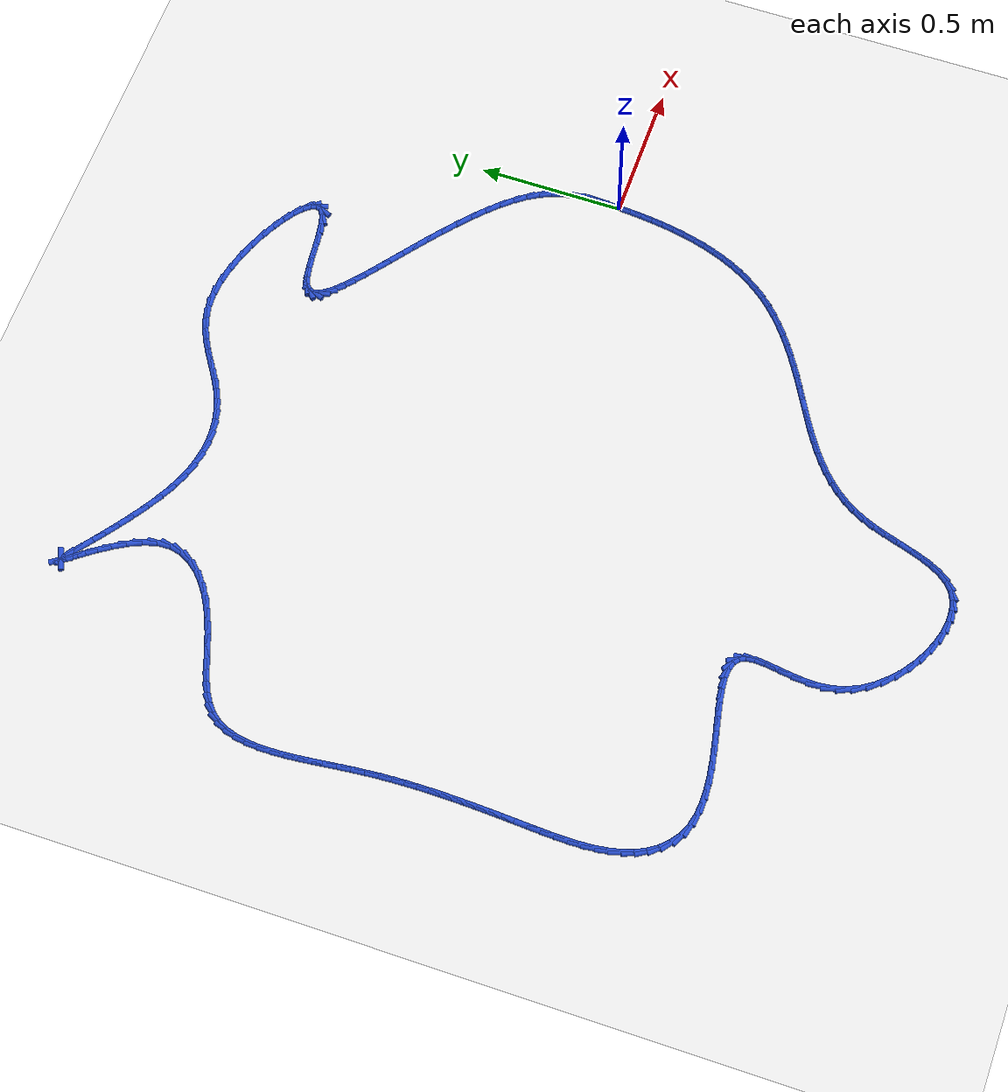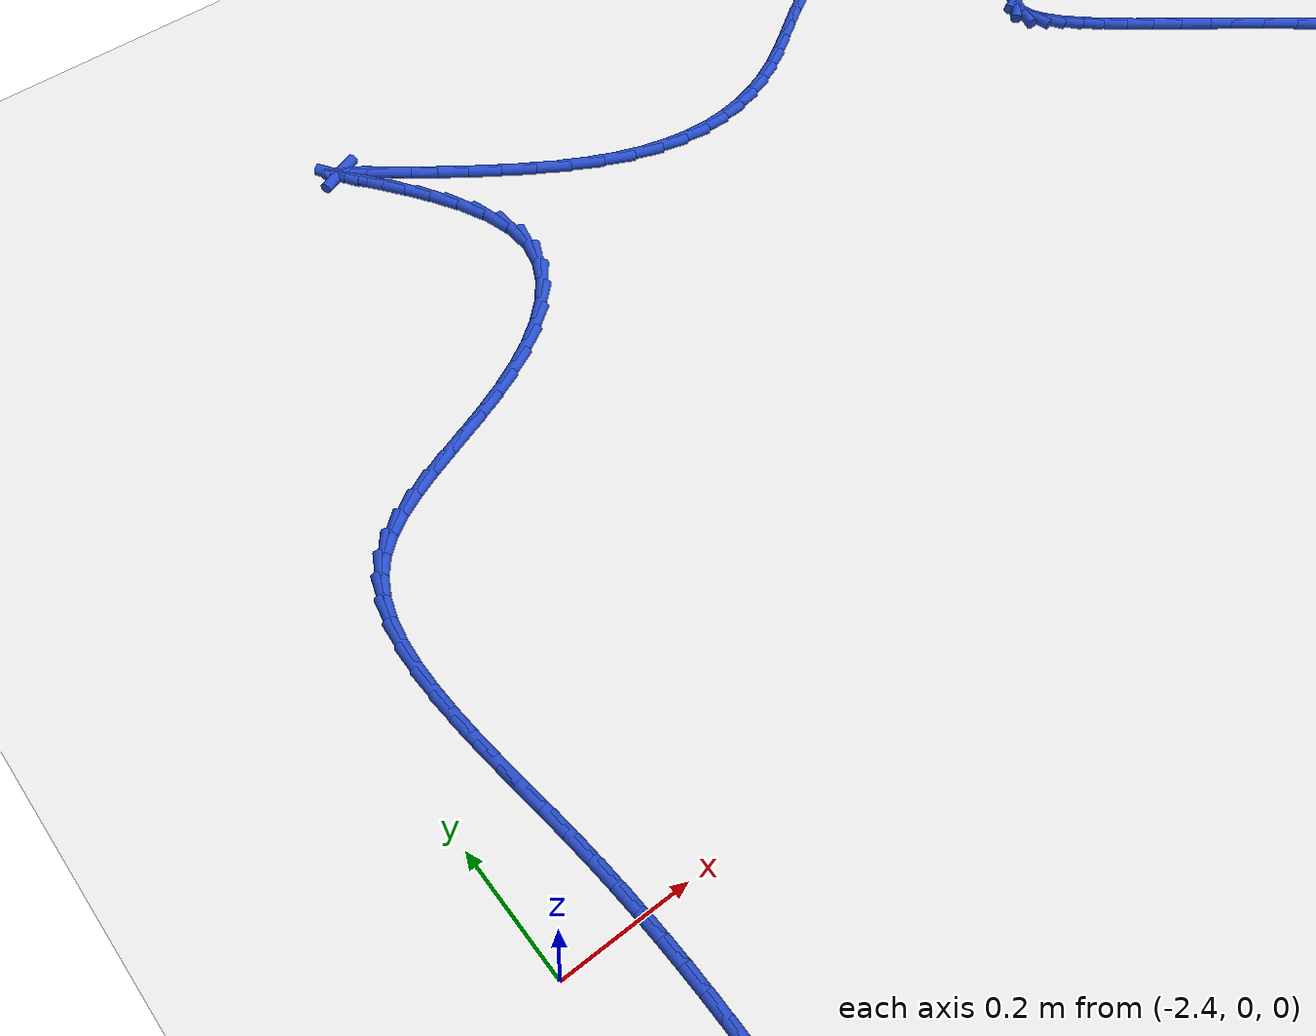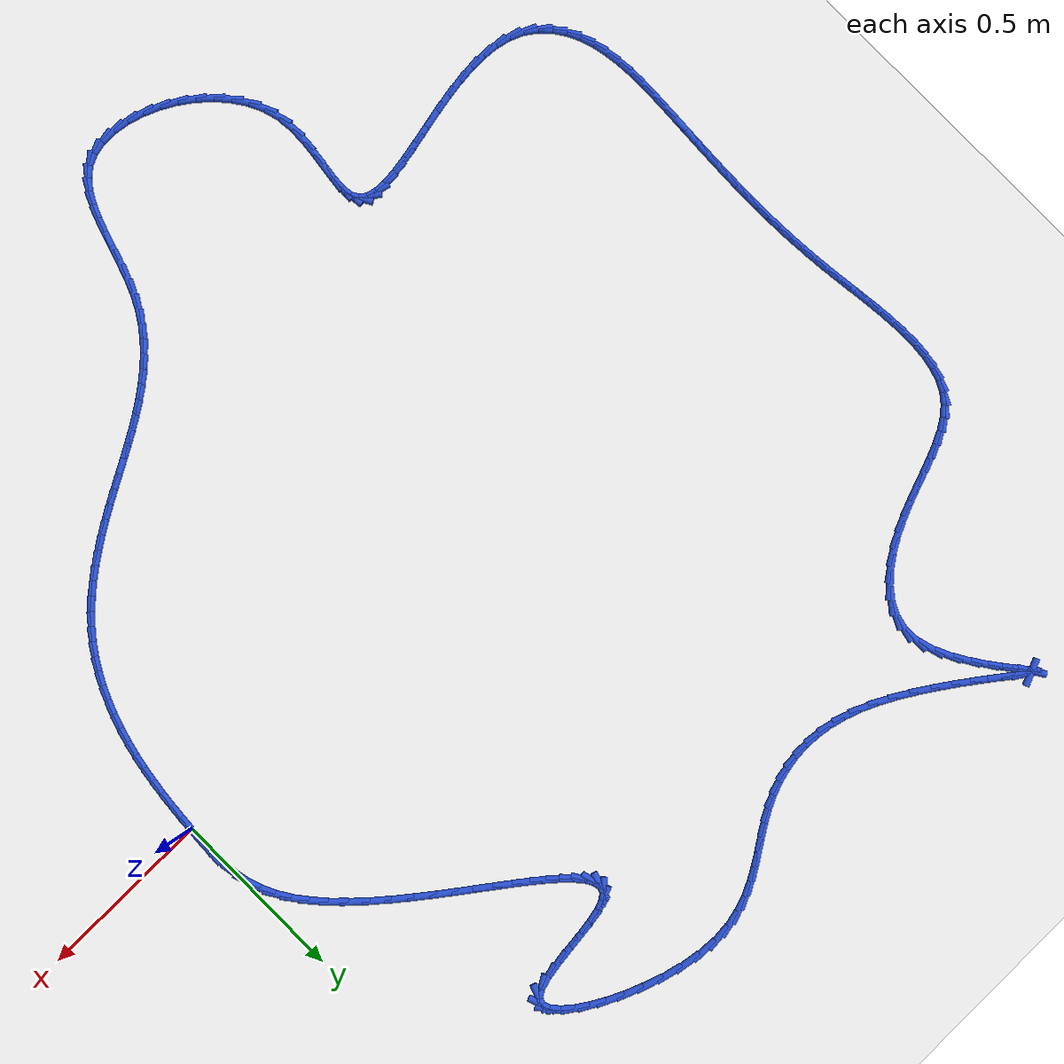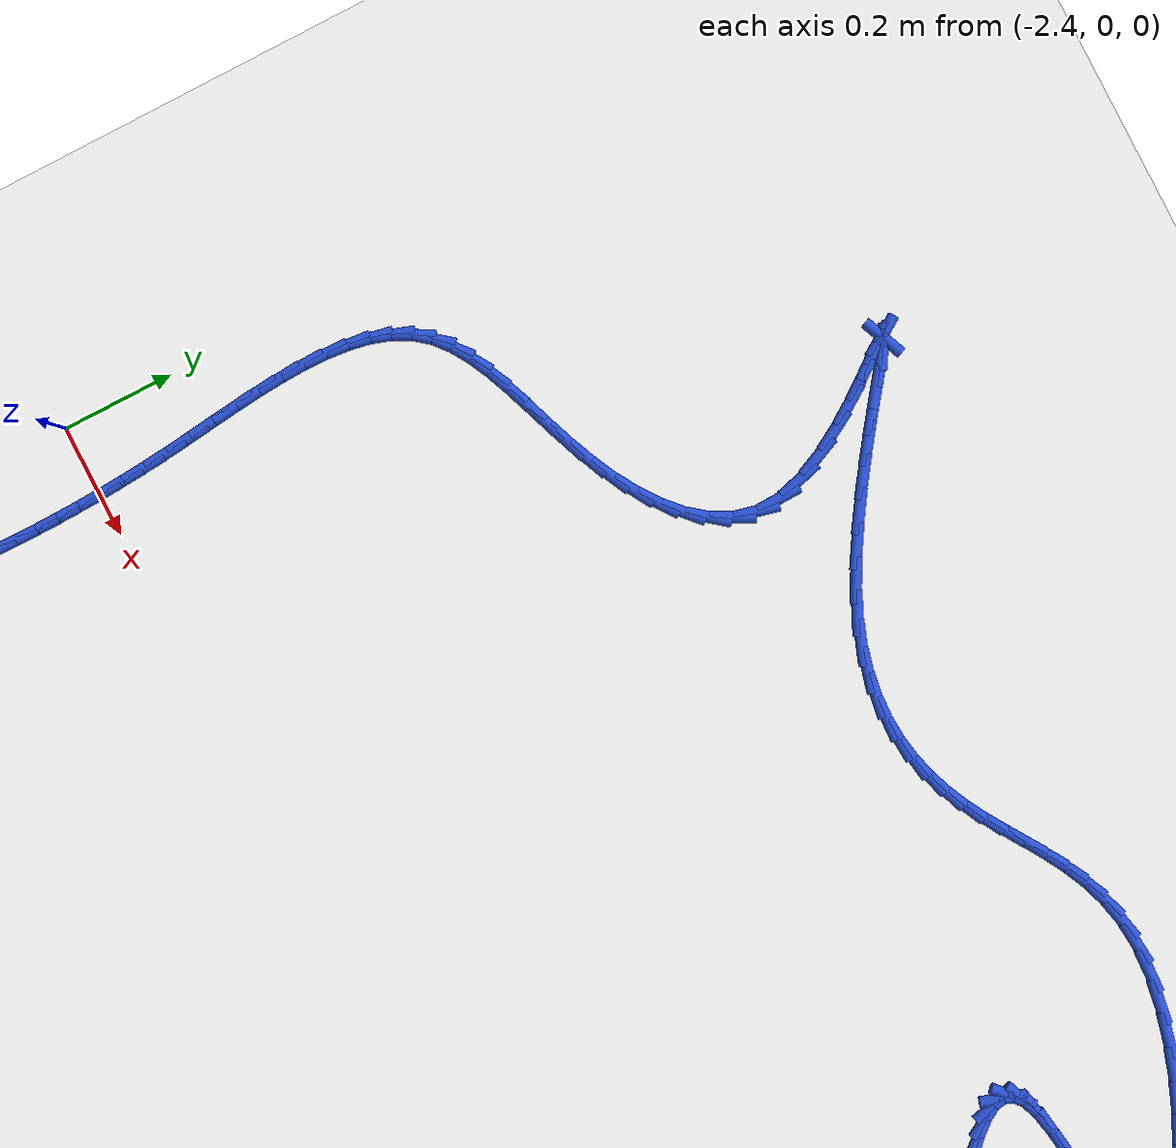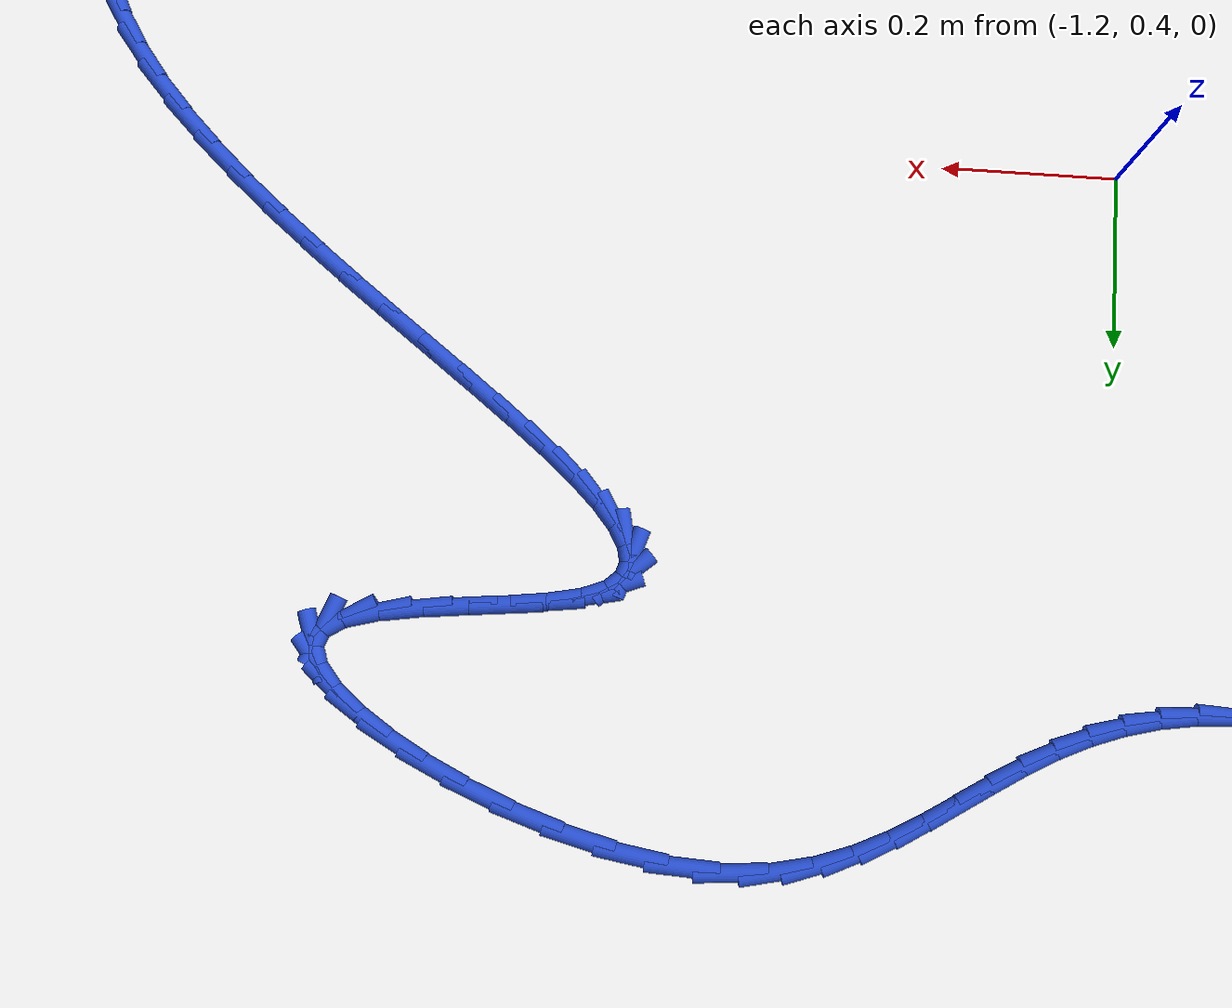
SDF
<sdf version="1.6">
 <world name="default">
  <light name="sun" type="directional">
   <pose>0 0 10 0 -0 0</pose>
   <diffuse>0.8 0.8 0.8 1</diffuse>
   <specular>0.2 0.2 0.2 1</specular>
   <attenuation>
    <range>1000</range>
    <constant>0.9</constant>
    <linear>0.01</linear>
    <quadratic>0.001</quadratic>
   </attenuation>
   <direction>-0.5 0.1 -0.9</direction>
  </light>
  <model name="ground_plane">
   <static>1</static>
   <link name="link">
    <collision name="collision">
     <geometry><plane><normal>0 0 1</normal><size>100 100</size></plane></geometry>
     <surface><friction><ode><mu>100</mu><mu2>50</mu2></ode></friction></surface>
    </collision>
    <visual name="visual">
     <cast_shadows>0</cast_shadows>
     <geometry><plane><normal>0 0 1</normal><size>100 100</size></plane></geometry>
     <material>
      <script><uri>file://media/materials/scripts/gazebo.material</uri><name>Gazebo/WhiteGlow</name></script>
     </material>
    </visual>
   </link>
  </model>
  <gravity>0 0 -9.8</gravity>
  <magnetic_field>6e-06 2.3e-05 -4.2e-05</magnetic_field>
  <atmosphere type="adiabatic"/>
  <physics name="default_physics" default="0" type="ode">
   <max_step_size>0.001</max_step_size>
   <real_time_factor>1</real_time_factor>
   <real_time_update_rate>1000</real_time_update_rate>
  </physics>
  <scene><ambient>0.4 0.4 0.4 1</ambient><background>0.7 0.7 0.7 1</background><shadows>1</shadows></scene>
  <spherical_coordinates>
   <surface_model>EARTH_WGS84</surface_model>
   <latitude_deg>0</latitude_deg>
   <longitude_deg>0</longitude_deg>
   <elevation>0</elevation>
   <heading_deg>0</heading_deg>
  </spherical_coordinates>
  <model name="line">
   <link name="link_0">
    <pose>-2.6454533008646308e-17 4.85722573273506e-17 0.01 0 1.57 1.509269195185731</pose>
    <collision name="collision">
     <geometry><cylinder><radius>0.01</radius><length>0.08</length></cylinder></geometry>
    </collision>
    <visual name="visual">
     <material>
      <script><name>Gazebo/Blue</name><uri>file://media/materials/scripts/gazebo.material</uri></script>
     </material>
     <geometry><cylinder><radius>0.01</radius><length>0.08</length></cylinder></geometry>
    </visual>
   </link>
   <link name="link_1">
    <pose>0.0025201213532394574 0.04090781477339782 0.01 0 1.57 1.5417251489490051</pose>
    <collision name="collision">
     <geometry><cylinder><radius>0.01</radius><length>0.08</length></cylinder></geometry>
    </collision>
    <visual name="visual">
     <material>
      <script><name>Gazebo/Blue</name><uri>file://media/materials/scripts/gazebo.material</uri></script>
     </material>
     <geometry><cylinder><radius>0.01</radius><length>0.08</length></cylinder></geometry>
    </visual>
   </link>
   <link name="link_2">
    <pose>0.00370807624145367 0.08175996791085728 0.01 0 1.57 -1.5446514620259824</pose>
    <collision name="collision">
     <geometry><cylinder><radius>0.01</radius><length>0.08</length></cylinder></geometry>
    </collision>
    <visual name="visual">
     <material>
      <script><name>Gazebo/Blue</name><uri>file://media/materials/scripts/gazebo.material</uri></script>
     </material>
     <geometry><cylinder><radius>0.01</radius><length>0.08</length></cylinder></geometry>
    </visual>
   </link>
   <link name="link_3">
    <pose>0.002640877953900527 0.12256932467615686 0.01 0 1.57 -1.4670650868832078</pose>
    <collision name="collision">
     <geometry><cylinder><radius>0.01</radius><length>0.08</length></cylinder></geometry>
    </collision>
    <visual name="visual">
     <material>
      <script><name>Gazebo/Blue</name><uri>file://media/materials/scripts/gazebo.material</uri></script>
     </material>
     <geometry><cylinder><radius>0.01</radius><length>0.08</length></cylinder></geometry>
    </visual>
   </link>
   <link name="link_4">
    <pose>-0.0016044602201620434 0.16334875033307514 0.01 0 1.57 -1.3688289097441755</pose>
    <collision name="collision">
     <geometry><cylinder><radius>0.01</radius><length>0.08</length></cylinder></geometry>
    </collision>
    <visual name="visual">
     <material>
      <script><name>Gazebo/Blue</name><uri>file://media/materials/scripts/gazebo.material</uri></script>
     </material>
     <geometry><cylinder><radius>0.01</radius><length>0.08</length></cylinder></geometry>
    </visual>
   </link>
   <link name="link_5">
    <pose>-0.00995092499147613 0.2041111101453905 0.01 0 1.57 -1.253811298840657</pose>
    <collision name="collision">
     <geometry><cylinder><radius>0.01</radius><length>0.08</length></cylinder></geometry>
    </collision>
    <visual name="visual">
     <material>
      <script><name>Gazebo/Blue</name><uri>file://media/materials/scripts/gazebo.material</uri></script>
     </material>
     <geometry><cylinder><radius>0.01</radius><length>0.08</length></cylinder></geometry>
    </visual>
   </link>
   <link name="link_6">
    <pose>-0.023321503070783803 0.24486926937688142 0.01 0 1.57 -1.1282854065230519</pose>
    <collision name="collision">
     <geometry><cylinder><radius>0.01</radius><length>0.08</length></cylinder></geometry>
    </collision>
    <visual name="visual">
     <material>
      <script><name>Gazebo/Blue</name><uri>file://media/materials/scripts/gazebo.material</uri></script>
     </material>
     <geometry><cylinder><radius>0.01</radius><length>0.08</length></cylinder></geometry>
    </visual>
   </link>
   <link name="link_7">
    <pose>-0.04263891654962168 0.2856360703587166 0.01 0 1.57 -1.0065701139669982</pose>
    <collision name="collision">
     <geometry><cylinder><radius>0.01</radius><length>0.08</length></cylinder></geometry>
    </collision>
    <visual name="visual">
     <material>
      <script><name>Gazebo/Blue</name><uri>file://media/materials/scripts/gazebo.material</uri></script>
     </material>
     <geometry><cylinder><radius>0.01</radius><length>0.08</length></cylinder></geometry>
    </visual>
   </link>
   <link name="link_8">
    <pose>-0.06843018685082376 0.3263900629412451 0.01 0 1.57 -0.9095853364182266</pose>
    <collision name="collision">
     <geometry><cylinder><radius>0.01</radius><length>0.08</length></cylinder></geometry>
    </collision>
    <visual name="visual">
     <material>
      <script><name>Gazebo/Blue</name><uri>file://media/materials/scripts/gazebo.material</uri></script>
     </material>
     <geometry><cylinder><radius>0.01</radius><length>0.08</length></cylinder></geometry>
    </visual>
   </link>
   <link name="link_9">
    <pose>-0.10003178403023383 0.3670066206014952 0.01 0 1.57 -0.8349249566194558</pose>
    <collision name="collision">
     <geometry><cylinder><radius>0.01</radius><length>0.08</length></cylinder></geometry>
    </collision>
    <visual name="visual">
     <material>
      <script><name>Gazebo/Blue</name><uri>file://media/materials/scripts/gazebo.material</uri></script>
     </material>
     <geometry><cylinder><radius>0.01</radius><length>0.08</length></cylinder></geometry>
    </visual>
   </link>
   <link name="link_10">
    <pose>-0.1365571817886406 0.4073417913545149 0.01 0 1.57 -0.7772857545090989</pose>
    <collision name="collision">
     <geometry><cylinder><radius>0.01</radius><length>0.08</length></cylinder></geometry>
    </collision>
    <visual name="visual">
     <material>
      <script><name>Gazebo/Blue</name><uri>file://media/materials/scripts/gazebo.material</uri></script>
     </material>
     <geometry><cylinder><radius>0.01</radius><length>0.08</length></cylinder></geometry>
    </visual>
   </link>
   <link name="link_11">
    <pose>-0.1771198538268327 0.4472516232153523 0.01 0 1.57 -0.7327956751561371</pose>
    <collision name="collision">
     <geometry><cylinder><radius>0.01</radius><length>0.08</length></cylinder></geometry>
    </collision>
    <visual name="visual">
     <material>
      <script><name>Gazebo/Blue</name><uri>file://media/materials/scripts/gazebo.material</uri></script>
     </material>
     <geometry><cylinder><radius>0.01</radius><length>0.08</length></cylinder></geometry>
    </visual>
   </link>
   <link name="link_12">
    <pose>-0.22083327384559892 0.4865921641990554 0.01 0 1.57 -0.6987373398845259</pose>
    <collision name="collision">
     <geometry><cylinder><radius>0.01</radius><length>0.08</length></cylinder></geometry>
    </collision>
    <visual name="visual">
     <material>
      <script><name>Gazebo/Blue</name><uri>file://media/materials/scripts/gazebo.material</uri></script>
     </material>
     <geometry><cylinder><radius>0.01</radius><length>0.08</length></cylinder></geometry>
    </visual>
   </link>
   <link name="link_13">
    <pose>-0.2668109155457279 0.5252194623206721 0.01 0 1.57 -0.6732691848513949</pose>
    <collision name="collision">
     <geometry><cylinder><radius>0.01</radius><length>0.08</length></cylinder></geometry>
    </collision>
    <visual name="visual">
     <material>
      <script><name>Gazebo/Blue</name><uri>file://media/materials/scripts/gazebo.material</uri></script>
     </material>
     <geometry><cylinder><radius>0.01</radius><length>0.08</length></cylinder></geometry>
    </visual>
   </link>
   <link name="link_14">
    <pose>-0.3141662526280081 0.5629895655952504 0.01 0 1.57 -0.6552221184754208</pose>
    <collision name="collision">
     <geometry><cylinder><radius>0.01</radius><length>0.08</length></cylinder></geometry>
    </collision>
    <visual name="visual">
     <material>
      <script><name>Gazebo/Blue</name><uri>file://media/materials/scripts/gazebo.material</uri></script>
     </material>
     <geometry><cylinder><radius>0.01</radius><length>0.08</length></cylinder></geometry>
    </visual>
   </link>
   <link name="link_15">
    <pose>-0.3620127587932287 0.5997585220378386 0.01 0 1.57 -0.6439796900205215</pose>
    <collision name="collision">
     <geometry><cylinder><radius>0.01</radius><length>0.08</length></cylinder></geometry>
    </collision>
    <visual name="visual">
     <material>
      <script><name>Gazebo/Blue</name><uri>file://media/materials/scripts/gazebo.material</uri></script>
     </material>
     <geometry><cylinder><radius>0.01</radius><length>0.08</length></cylinder></geometry>
    </visual>
   </link>
   <link name="link_16">
    <pose>-0.4094639077421781 0.6353823796634845 0.01 0 1.57 -0.6394391074112148</pose>
    <collision name="collision">
     <geometry><cylinder><radius>0.01</radius><length>0.08</length></cylinder></geometry>
    </collision>
    <visual name="visual">
     <material>
      <script><name>Gazebo/Blue</name><uri>file://media/materials/scripts/gazebo.material</uri></script>
     </material>
     <geometry><cylinder><radius>0.01</radius><length>0.08</length></cylinder></geometry>
    </visual>
   </link>
   <link name="link_17">
    <pose>-0.45563317317564506 0.6697171864872364 0.01 0 1.57 -0.6420619470846901</pose>
    <collision name="collision">
     <geometry><cylinder><radius>0.01</radius><length>0.08</length></cylinder></geometry>
    </collision>
    <visual name="visual">
     <material>
      <script><name>Gazebo/Blue</name><uri>file://media/materials/scripts/gazebo.material</uri></script>
     </material>
     <geometry><cylinder><radius>0.01</radius><length>0.08</length></cylinder></geometry>
    </visual>
   </link>
   <link name="link_18">
    <pose>-0.4996340287944181 0.702618990524142 0.01 0 1.57 -0.6530510027040978</pose>
    <collision name="collision">
     <geometry><cylinder><radius>0.01</radius><length>0.08</length></cylinder></geometry>
    </collision>
    <visual name="visual">
     <material>
      <script><name>Gazebo/Blue</name><uri>file://media/materials/scripts/gazebo.material</uri></script>
     </material>
     <geometry><cylinder><radius>0.01</radius><length>0.08</length></cylinder></geometry>
    </visual>
   </link>
   <link name="link_19">
    <pose>-0.5405799482992861 0.7339438397892496 0.01 0 1.57 -0.6747471516450356</pose>
    <collision name="collision">
     <geometry><cylinder><radius>0.01</radius><length>0.08</length></cylinder></geometry>
    </collision>
    <visual name="visual">
     <material>
      <script><name>Gazebo/Blue</name><uri>file://media/materials/scripts/gazebo.material</uri></script>
     </material>
     <geometry><cylinder><radius>0.01</radius><length>0.08</length></cylinder></geometry>
    </visual>
   </link>
   <link name="link_20">
    <pose>-0.5775844053910376 0.7635477822976069 0.01 0 1.57 -0.7114724786341811</pose>
    <collision name="collision">
     <geometry><cylinder><radius>0.01</radius><length>0.08</length></cylinder></geometry>
    </collision>
    <visual name="visual">
     <material>
      <script><name>Gazebo/Blue</name><uri>file://media/materials/scripts/gazebo.material</uri></script>
     </material>
     <geometry><cylinder><radius>0.01</radius><length>0.08</length></cylinder></geometry>
    </visual>
   </link>
   <link name="link_21">
    <pose>-0.6097608737704615 0.791286866064262 0.01 0 1.57 -0.7713801294628543</pose>
    <collision name="collision">
     <geometry><cylinder><radius>0.01</radius><length>0.08</length></cylinder></geometry>
    </collision>
    <visual name="visual">
     <material>
      <script><name>Gazebo/Blue</name><uri>file://media/materials/scripts/gazebo.material</uri></script>
     </material>
     <geometry><cylinder><radius>0.01</radius><length>0.08</length></cylinder></geometry>
    </visual>
   </link>
   <link name="link_22">
    <pose>-0.6362228271383463 0.8170171391042631 0.01 0 1.57 -0.8707504512054686</pose>
    <collision name="collision">
     <geometry><cylinder><radius>0.01</radius><length>0.08</length></cylinder></geometry>
    </collision>
    <visual name="visual">
     <material>
      <script><name>Gazebo/Blue</name><uri>file://media/materials/scripts/gazebo.material</uri></script>
     </material>
     <geometry><cylinder><radius>0.01</radius><length>0.08</length></cylinder></geometry>
    </visual>
   </link>
   <link name="link_23">
    <pose>-0.6560837391954809 0.8405946494326584 0.01 0 1.57 -1.0441413518200124</pose>
    <collision name="collision">
     <geometry><cylinder><radius>0.01</radius><length>0.08</length></cylinder></geometry>
    </collision>
    <visual name="visual">
     <material>
      <script><name>Gazebo/Blue</name><uri>file://media/materials/scripts/gazebo.material</uri></script>
     </material>
     <geometry><cylinder><radius>0.01</radius><length>0.08</length></cylinder></geometry>
    </visual>
   </link>
   <link name="link_24">
    <pose>-0.6684570836426538 0.8618754450644954 0.01 0 1.57 -1.3616281441238216</pose>
    <collision name="collision">
     <geometry><cylinder><radius>0.01</radius><length>0.08</length></cylinder></geometry>
    </collision>
    <visual name="visual">
     <material>
      <script><name>Gazebo/Blue</name><uri>file://media/materials/scripts/gazebo.material</uri></script>
     </material>
     <geometry><cylinder><radius>0.01</radius><length>0.08</length></cylinder></geometry>
    </visual>
   </link>
   <link name="link_25">
    <pose>-0.6724563341806539 0.8807155740148225 0.01 0 1.57 1.2577706961210036</pose>
    <collision name="collision">
     <geometry><cylinder><radius>0.01</radius><length>0.08</length></cylinder></geometry>
    </collision>
    <visual name="visual">
     <material>
      <script><name>Gazebo/Blue</name><uri>file://media/materials/scripts/gazebo.material</uri></script>
     </material>
     <geometry><cylinder><radius>0.01</radius><length>0.08</length></cylinder></geometry>
    </visual>
   </link>
   <link name="link_26">
    <pose>-0.6671949645102694 0.8969710842986875 0.01 0 1.57 0.7204629087555768</pose>
    <collision name="collision">
     <geometry><cylinder><radius>0.01</radius><length>0.08</length></cylinder></geometry>
    </collision>
    <visual name="visual">
     <material>
      <script><name>Gazebo/Blue</name><uri>file://media/materials/scripts/gazebo.material</uri></script>
     </material>
     <geometry><cylinder><radius>0.01</radius><length>0.08</length></cylinder></geometry>
    </visual>
   </link>
   <link name="link_27">
    <pose>-0.6517864483322895 0.9104980239311387 0.01 0 1.57 0.38303491947691204</pose>
    <collision name="collision">
     <geometry><cylinder><radius>0.01</radius><length>0.08</length></cylinder></geometry>
    </collision>
    <visual name="visual">
     <material>
      <script><name>Gazebo/Blue</name><uri>file://media/materials/scripts/gazebo.material</uri></script>
     </material>
     <geometry><cylinder><radius>0.01</radius><length>0.08</length></cylinder></geometry>
    </visual>
   </link>
   <link name="link_28">
    <pose>-0.6253444046064736 0.9211524775095848 0.01 0 1.57 0.20779085892381952</pose>
    <collision name="collision">
     <geometry><cylinder><radius>0.01</radius><length>0.08</length></cylinder></geometry>
    </collision>
    <visual name="visual">
     <material>
      <script><name>Gazebo/Blue</name><uri>file://media/materials/scripts/gazebo.material</uri></script>
     </material>
     <geometry><cylinder><radius>0.01</radius><length>0.08</length></cylinder></geometry>
    </visual>
   </link>
   <link name="link_29">
    <pose>-0.5879549521777492 0.9290354462904789 0.01 0 1.57 0.13356316622591824</pose>
    <collision name="collision">
     <geometry><cylinder><radius>0.01</radius><length>0.08</length></cylinder></geometry>
    </collision>
    <visual name="visual">
     <material>
      <script><name>Gazebo/Blue</name><uri>file://media/materials/scripts/gazebo.material</uri></script>
     </material>
     <geometry><cylinder><radius>0.01</radius><length>0.08</length></cylinder></geometry>
    </visual>
   </link>
   <link name="link_30">
    <pose>-0.5429942558055588 0.935076504433749 0.01 0 1.57 0.10901081676127165</pose>
    <collision name="collision">
     <geometry><cylinder><radius>0.01</radius><length>0.08</length></cylinder></geometry>
    </collision>
    <visual name="visual">
     <material>
      <script><name>Gazebo/Blue</name><uri>file://media/materials/scripts/gazebo.material</uri></script>
     </material>
     <geometry><cylinder><radius>0.01</radius><length>0.08</length></cylinder></geometry>
    </visual>
   </link>
   <link name="link_31">
    <pose>-0.49453354161133917 0.9403802719879729 0.01 0 1.57 0.11787151251198527</pose>
    <collision name="collision">
     <geometry><cylinder><radius>0.01</radius><length>0.08</length></cylinder></geometry>
    </collision>
    <visual name="visual">
     <material>
      <script><name>Gazebo/Blue</name><uri>file://media/materials/scripts/gazebo.material</uri></script>
     </material>
     <geometry><cylinder><radius>0.01</radius><length>0.08</length></cylinder></geometry>
    </visual>
   </link>
   <link name="link_32">
    <pose>-0.4466440357165279 0.946051369001728 0.01 0 1.57 0.163690481918927</pose>
    <collision name="collision">
     <geometry><cylinder><radius>0.01</radius><length>0.08</length></cylinder></geometry>
    </collision>
    <visual name="visual">
     <material>
      <script><name>Gazebo/Blue</name><uri>file://media/materials/scripts/gazebo.material</uri></script>
     </material>
     <geometry><cylinder><radius>0.01</radius><length>0.08</length></cylinder></geometry>
    </visual>
   </link>
   <link name="link_33">
    <pose>-0.4033969642425618 0.9531944155235916 0.01 0 1.57 0.274357813742018</pose>
    <collision name="collision">
     <geometry><cylinder><radius>0.01</radius><length>0.08</length></cylinder></geometry>
    </collision>
    <visual name="visual">
     <material>
      <script><name>Gazebo/Blue</name><uri>file://media/materials/scripts/gazebo.material</uri></script>
     </material>
     <geometry><cylinder><radius>0.01</radius><length>0.08</length></cylinder></geometry>
    </visual>
   </link>
   <link name="link_34">
    <pose>-0.36886355331087833 0.9629140316021412 0.01 0 1.57 0.5518086828791245</pose>
    <collision name="collision">
     <geometry><cylinder><radius>0.01</radius><length>0.08</length></cylinder></geometry>
    </collision>
    <visual name="visual">
     <material>
      <script><name>Gazebo/Blue</name><uri>file://media/materials/scripts/gazebo.material</uri></script>
     </material>
     <geometry><cylinder><radius>0.01</radius><length>0.08</length></cylinder></geometry>
    </visual>
   </link>
   <link name="link_35">
    <pose>-0.34710216236399644 0.9763102686144918 0.01 0 1.57 1.205866641085095</pose>
    <collision name="collision">
     <geometry><cylinder><radius>0.01</radius><length>0.08</length></cylinder></geometry>
    </collision>
    <visual name="visual">
     <material>
      <script><name>Gazebo/Blue</name><uri>file://media/materials/scripts/gazebo.material</uri></script>
     </material>
     <geometry><cylinder><radius>0.01</radius><length>0.08</length></cylinder></geometry>
    </visual>
   </link>
   <link name="link_36">
    <pose>-0.3403996668560106 0.9938541633804235 0.01 0 1.57 -1.2441025698154802</pose>
    <collision name="collision">
     <geometry><cylinder><radius>0.01</radius><length>0.08</length></cylinder></geometry>
    </collision>
    <visual name="visual">
     <material>
      <script><name>Gazebo/Blue</name><uri>file://media/materials/scripts/gazebo.material</uri></script>
     </material>
     <geometry><cylinder><radius>0.01</radius><length>0.08</length></cylinder></geometry>
    </visual>
   </link>
   <link name="link_37">
    <pose>-0.3474805207233217 1.0147518160854392 0.01 0 1.57 -0.8826733075945599</pose>
    <collision name="collision">
     <geometry><cylinder><radius>0.01</radius><length>0.08</length></cylinder></geometry>
    </collision>
    <visual name="visual">
     <material>
      <script><name>Gazebo/Blue</name><uri>file://media/materials/scripts/gazebo.material</uri></script>
     </material>
     <geometry><cylinder><radius>0.01</radius><length>0.08</length></cylinder></geometry>
    </visual>
   </link>
   <link name="link_38">
    <pose>-0.3666423310184498 1.0380577630818557 0.01 0 1.57 -0.6977633048910638</pose>
    <collision name="collision">
     <geometry><cylinder><radius>0.01</radius><length>0.08</length></cylinder></geometry>
    </collision>
    <visual name="visual">
     <material>
      <script><name>Gazebo/Blue</name><uri>file://media/materials/scripts/gazebo.material</uri></script>
     </material>
     <geometry><cylinder><radius>0.01</radius><length>0.08</length></cylinder></geometry>
    </visual>
   </link>
   <link name="link_39">
    <pose>-0.3961827047939155 1.0628265407219906 0.01 0 1.57 -0.584524539721005</pose>
    <collision name="collision">
     <geometry><cylinder><radius>0.01</radius><length>0.08</length></cylinder></geometry>
    </collision>
    <visual name="visual">
     <material>
      <script><name>Gazebo/Blue</name><uri>file://media/materials/scripts/gazebo.material</uri></script>
     </material>
     <geometry><cylinder><radius>0.01</radius><length>0.08</length></cylinder></geometry>
    </visual>
   </link>
   <link name="link_40">
    <pose>-0.4343992491022391 1.0881126853581606 0.01 0 1.57 -0.5029004792633465</pose>
    <collision name="collision">
     <geometry><cylinder><radius>0.01</radius><length>0.08</length></cylinder></geometry>
    </collision>
    <visual name="visual">
     <material>
      <script><name>Gazebo/Blue</name><uri>file://media/materials/scripts/gazebo.material</uri></script>
     </material>
     <geometry><cylinder><radius>0.01</radius><length>0.08</length></cylinder></geometry>
    </visual>
   </link>
   <link name="link_41">
    <pose>-0.4795895709959406 1.1129707333426824 0.01 0 1.57 -0.4355801476792492</pose>
    <collision name="collision">
     <geometry><cylinder><radius>0.01</radius><length>0.08</length></cylinder></geometry>
    </collision>
    <visual name="visual">
     <material>
      <script><name>Gazebo/Blue</name><uri>file://media/materials/scripts/gazebo.material</uri></script>
     </material>
     <geometry><cylinder><radius>0.01</radius><length>0.08</length></cylinder></geometry>
    </visual>
   </link>
   <link name="link_42">
    <pose>-0.5300512775275408 1.136455221027873 0.01 0 1.57 -0.373357093637007</pose>
    <collision name="collision">
     <geometry><cylinder><radius>0.01</radius><length>0.08</length></cylinder></geometry>
    </collision>
    <visual name="visual">
     <material>
      <script><name>Gazebo/Blue</name><uri>file://media/materials/scripts/gazebo.material</uri></script>
     </material>
     <geometry><cylinder><radius>0.01</radius><length>0.08</length></cylinder></geometry>
    </visual>
   </link>
   <link name="link_43">
    <pose>-0.5840819757495601 1.1576206847660502 0.01 0 1.57 -0.30992754458472</pose>
    <collision name="collision">
     <geometry><cylinder><radius>0.01</radius><length>0.08</length></cylinder></geometry>
    </collision>
    <visual name="visual">
     <material>
      <script><name>Gazebo/Blue</name><uri>file://media/materials/scripts/gazebo.material</uri></script>
     </material>
     <geometry><cylinder><radius>0.01</radius><length>0.08</length></cylinder></geometry>
    </visual>
   </link>
   <link name="link_44">
    <pose>-0.6399792727145184 1.1755216609095298 0.01 0 1.57 -0.23952600085875478</pose>
    <collision name="collision">
     <geometry><cylinder><radius>0.01</radius><length>0.08</length></cylinder></geometry>
    </collision>
    <visual name="visual">
     <material>
      <script><name>Gazebo/Blue</name><uri>file://media/materials/scripts/gazebo.material</uri></script>
     </material>
     <geometry><cylinder><radius>0.01</radius><length>0.08</length></cylinder></geometry>
    </visual>
   </link>
   <link name="link_45">
    <pose>-0.6960407754749363 1.1892126858106289 0.01 0 1.57 -0.15528930946947003</pose>
    <collision name="collision">
     <geometry><cylinder><radius>0.01</radius><length>0.08</length></cylinder></geometry>
    </collision>
    <visual name="visual">
     <material>
      <script><name>Gazebo/Blue</name><uri>file://media/materials/scripts/gazebo.material</uri></script>
     </material>
     <geometry><cylinder><radius>0.01</radius><length>0.08</length></cylinder></geometry>
    </visual>
   </link>
   <link name="link_46">
    <pose>-0.750564091083334 1.197748295821665 0.01 0 1.57 -0.047489943298552544</pose>
    <collision name="collision">
     <geometry><cylinder><radius>0.01</radius><length>0.08</length></cylinder></geometry>
    </collision>
    <visual name="visual">
     <material>
      <script><name>Gazebo/Blue</name><uri>file://media/materials/scripts/gazebo.material</uri></script>
     </material>
     <geometry><cylinder><radius>0.01</radius><length>0.08</length></cylinder></geometry>
    </visual>
   </link>
   <link name="link_47">
    <pose>-0.8018499429143217 1.2001856906405788 0.01 0 1.57 0.08569642645641715</pose>
    <collision name="collision">
     <geometry><cylinder><radius>0.01</radius><length>0.08</length></cylinder></geometry>
    </collision>
    <visual name="visual">
     <material>
      <script><name>Gazebo/Blue</name><uri>file://media/materials/scripts/gazebo.material</uri></script>
     </material>
     <geometry><cylinder><radius>0.01</radius><length>0.08</length></cylinder></geometry>
    </visual>
   </link>
   <link name="link_48">
    <pose>-0.8488602793259842 1.1961471818554312 0.01 0 1.57 0.21948933627469472</pose>
    <collision name="collision">
     <geometry><cylinder><radius>0.01</radius><length>0.08</length></cylinder></geometry>
    </collision>
    <visual name="visual">
     <material>
      <script><name>Gazebo/Blue</name><uri>file://media/materials/scripts/gazebo.material</uri></script>
     </material>
     <geometry><cylinder><radius>0.01</radius><length>0.08</length></cylinder></geometry>
    </visual>
   </link>
   <link name="link_49">
    <pose>-0.8920326063614578 1.1865161574098626 0.01 0 1.57 0.3406687532184814</pose>
    <collision name="collision">
     <geometry><cylinder><radius>0.01</radius><length>0.08</length></cylinder></geometry>
    </collision>
    <visual name="visual">
     <material>
      <script><name>Gazebo/Blue</name><uri>file://media/materials/scripts/gazebo.material</uri></script>
     </material>
     <geometry><cylinder><radius>0.01</radius><length>0.08</length></cylinder></geometry>
    </visual>
   </link>
   <link name="link_50">
    <pose>-0.9320041256906857 1.1723466738942439 0.01 0 1.57 0.44093984602337905</pose>
    <collision name="collision">
     <geometry><cylinder><radius>0.01</radius><length>0.08</length></cylinder></geometry>
    </collision>
    <visual name="visual">
     <material>
      <script><name>Gazebo/Blue</name><uri>file://media/materials/scripts/gazebo.material</uri></script>
     </material>
     <geometry><cylinder><radius>0.01</radius><length>0.08</length></cylinder></geometry>
    </visual>
   </link>
   <link name="link_51">
    <pose>-0.9694120389836114 1.154692787898946 0.01 0 1.57 0.5150804778031776</pose>
    <collision name="collision">
     <geometry><cylinder><radius>0.01</radius><length>0.08</length></cylinder></geometry>
    </collision>
    <visual name="visual">
     <material>
      <script><name>Gazebo/Blue</name><uri>file://media/materials/scripts/gazebo.material</uri></script>
     </material>
     <geometry><cylinder><radius>0.01</radius><length>0.08</length></cylinder></geometry>
    </visual>
   </link>
   <link name="link_52">
    <pose>-1.0048935479101777 1.134608556014339 0.01 0 1.57 0.560496793148033</pose>
    <collision name="collision">
     <geometry><cylinder><radius>0.01</radius><length>0.08</length></cylinder></geometry>
    </collision>
    <visual name="visual">
     <material>
      <script><name>Gazebo/Blue</name><uri>file://media/materials/scripts/gazebo.material</uri></script>
     </material>
     <geometry><cylinder><radius>0.01</radius><length>0.08</length></cylinder></geometry>
    </visual>
   </link>
   <link name="link_53">
    <pose>-1.0390858541403287 1.1131480348307945 0.01 0 1.57 0.5759885363308357</pose>
    <collision name="collision">
     <geometry><cylinder><radius>0.01</radius><length>0.08</length></cylinder></geometry>
    </collision>
    <visual name="visual">
     <material>
      <script><name>Gazebo/Blue</name><uri>file://media/materials/scripts/gazebo.material</uri></script>
     </material>
     <geometry><cylinder><radius>0.01</radius><length>0.08</length></cylinder></geometry>
    </visual>
   </link>
   <link name="link_54">
    <pose>-1.0726261593440072 1.0913652809386825 0.01 0 1.57 0.560687657962343</pose>
    <collision name="collision">
     <geometry><cylinder><radius>0.01</radius><length>0.08</length></cylinder></geometry>
    </collision>
    <visual name="visual">
     <material>
      <script><name>Gazebo/Blue</name><uri>file://media/materials/scripts/gazebo.material</uri></script>
     </material>
     <geometry><cylinder><radius>0.01</radius><length>0.08</length></cylinder></geometry>
    </visual>
   </link>
   <link name="link_55">
    <pose>-1.106151665191157 1.0703143509283741 0.01 0 1.57 0.5136627318660358</pose>
    <collision name="collision">
     <geometry><cylinder><radius>0.01</radius><length>0.08</length></cylinder></geometry>
    </collision>
    <visual name="visual">
     <material>
      <script><name>Gazebo/Blue</name><uri>file://media/materials/scripts/gazebo.material</uri></script>
     </material>
     <geometry><cylinder><radius>0.01</radius><length>0.08</length></cylinder></geometry>
    </visual>
   </link>
   <link name="link_56">
    <pose>-1.1402993432505182 1.0510490045870344 0.01 0 1.57 0.4398864103742831</pose>
    <collision name="collision">
     <geometry><cylinder><radius>0.01</radius><length>0.08</length></cylinder></geometry>
    </collision>
    <visual name="visual">
     <material>
      <script><name>Gazebo/Blue</name><uri>file://media/materials/scripts/gazebo.material</uri></script>
     </material>
     <geometry><cylinder><radius>0.01</radius><length>0.08</length></cylinder></geometry>
    </visual>
   </link>
   <link name="link_57">
    <pose>-1.1755710197870393 1.0344486803211155 0.01 0 1.57 0.3545110695305239</pose>
    <collision name="collision">
     <geometry><cylinder><radius>0.01</radius><length>0.08</length></cylinder></geometry>
    </collision>
    <visual name="visual">
     <material>
      <script><name>Gazebo/Blue</name><uri>file://media/materials/scripts/gazebo.material</uri></script>
     </material>
     <geometry><cylinder><radius>0.01</radius><length>0.08</length></cylinder></geometry>
    </visual>
   </link>
   <link name="link_58">
    <pose>-1.2121060496302407 1.0209252714628494 0.01 0 1.57 0.2608852014860669</pose>
    <collision name="collision">
     <geometry><cylinder><radius>0.01</radius><length>0.08</length></cylinder></geometry>
    </collision>
    <visual name="visual">
     <material>
      <script><name>Gazebo/Blue</name><uri>file://media/materials/scripts/gazebo.material</uri></script>
     </material>
     <geometry><cylinder><radius>0.01</radius><length>0.08</length></cylinder></geometry>
    </visual>
   </link>
   <link name="link_59">
    <pose>-1.2499836514662708 1.010813102866321 0.01 0 1.57 0.16060725590039027</pose>
    <collision name="collision">
     <geometry><cylinder><radius>0.01</radius><length>0.08</length></cylinder></geometry>
    </collision>
    <visual name="visual">
     <material>
      <script><name>Gazebo/Blue</name><uri>file://media/materials/scripts/gazebo.material</uri></script>
     </material>
     <geometry><cylinder><radius>0.01</radius><length>0.08</length></cylinder></geometry>
    </visual>
   </link>
   <link name="link_60">
    <pose>-1.2892830439812752 1.0044464993856144 0.01 0 1.57 0.055987773939713166</pose>
    <collision name="collision">
     <geometry><cylinder><radius>0.01</radius><length>0.08</length></cylinder></geometry>
    </collision>
    <visual name="visual">
     <material>
      <script><name>Gazebo/Blue</name><uri>file://media/materials/scripts/gazebo.material</uri></script>
     </material>
     <geometry><cylinder><radius>0.01</radius><length>0.08</length></cylinder></geometry>
    </visual>
   </link>
   <link name="link_61">
    <pose>-1.3300834458614017 1.0021597858748152 0.01 0 1.57 -0.05015774647665107</pose>
    <collision name="collision">
     <geometry><cylinder><radius>0.01</radius><length>0.08</length></cylinder></geometry>
    </collision>
    <visual name="visual">
     <material>
      <script><name>Gazebo/Blue</name><uri>file://media/materials/scripts/gazebo.material</uri></script>
     </material>
     <geometry><cylinder><radius>0.01</radius><length>0.08</length></cylinder></geometry>
    </visual>
   </link>
   <link name="link_62">
    <pose>-1.3724640757927964 1.0042872871880086 0.01 0 1.57 -0.154881014318404</pose>
    <collision name="collision">
     <geometry><cylinder><radius>0.01</radius><length>0.08</length></cylinder></geometry>
    </collision>
    <visual name="visual">
     <material>
      <script><name>Gazebo/Blue</name><uri>file://media/materials/scripts/gazebo.material</uri></script>
     </material>
     <geometry><cylinder><radius>0.01</radius><length>0.08</length></cylinder></geometry>
    </visual>
   </link>
   <link name="link_63">
    <pose>-1.4165041524616062 1.011163328179279 0.01 0 1.57 -0.25552238043071607</pose>
    <collision name="collision">
     <geometry><cylinder><radius>0.01</radius><length>0.08</length></cylinder></geometry>
    </collision>
    <visual name="visual">
     <material>
      <script><name>Gazebo/Blue</name><uri>file://media/materials/scripts/gazebo.material</uri></script>
     </material>
     <geometry><cylinder><radius>0.01</radius><length>0.08</length></cylinder></geometry>
    </visual>
   </link>
   <link name="link_64">
    <pose>-1.4622828945539783 1.0231222337027115 0.01 0 1.57 -0.35003652410434044</pose>
    <collision name="collision">
     <geometry><cylinder><radius>0.01</radius><length>0.08</length></cylinder></geometry>
    </collision>
    <visual name="visual">
     <material>
      <script><name>Gazebo/Blue</name><uri>file://media/materials/scripts/gazebo.material</uri></script>
     </material>
     <geometry><cylinder><radius>0.01</radius><length>0.08</length></cylinder></geometry>
    </visual>
   </link>
   <link name="link_65">
    <pose>-1.509879520756059 1.0404983286123908 0.01 0 1.57 -0.43590057355352124</pose>
    <collision name="collision">
     <geometry><cylinder><radius>0.01</radius><length>0.08</length></cylinder></geometry>
    </collision>
    <visual name="visual">
     <material>
      <script><name>Gazebo/Blue</name><uri>file://media/materials/scripts/gazebo.material</uri></script>
     </material>
     <geometry><cylinder><radius>0.01</radius><length>0.08</length></cylinder></geometry>
    </visual>
   </link>
   <link name="link_66">
    <pose>-1.5592972686204927 1.0635162332546528 0.01 0 1.57 -0.5027985200760697</pose>
    <collision name="collision">
     <geometry><cylinder><radius>0.01</radius><length>0.08</length></cylinder></geometry>
    </collision>
    <visual name="visual">
     <material>
      <script><name>Gazebo/Blue</name><uri>file://media/materials/scripts/gazebo.material</uri></script>
     </material>
     <geometry><cylinder><radius>0.01</radius><length>0.08</length></cylinder></geometry>
    </visual>
   </link>
   <link name="link_67">
    <pose>-1.6097516355563133 1.0912631982011933 0.01 0 1.57 -0.5512653810575215</pose>
    <collision name="collision">
     <geometry><cylinder><radius>0.01</radius><length>0.08</length></cylinder></geometry>
    </collision>
    <visual name="visual">
     <material>
      <script><name>Gazebo/Blue</name><uri>file://media/materials/scripts/gazebo.material</uri></script>
     </material>
     <geometry><cylinder><radius>0.01</radius><length>0.08</length></cylinder></geometry>
    </visual>
   </link>
   <link name="link_68">
    <pose>-1.6599918701969307 1.1221532859563463 0.01 0 1.57 -0.5869463190346283</pose>
    <collision name="collision">
     <geometry><cylinder><radius>0.01</radius><length>0.08</length></cylinder></geometry>
    </collision>
    <visual name="visual">
     <material>
      <script><name>Gazebo/Blue</name><uri>file://media/materials/scripts/gazebo.material</uri></script>
     </material>
     <geometry><cylinder><radius>0.01</radius><length>0.08</length></cylinder></geometry>
    </visual>
   </link>
   <link name="link_69">
    <pose>-1.7087611356379866 1.1545917724889714 0.01 0 1.57 -0.6131000767120406</pose>
    <collision name="collision">
     <geometry><cylinder><radius>0.01</radius><length>0.08</length></cylinder></geometry>
    </collision>
    <visual name="visual">
     <material>
      <script><name>Gazebo/Blue</name><uri>file://media/materials/scripts/gazebo.material</uri></script>
     </material>
     <geometry><cylinder><radius>0.01</radius><length>0.08</length></cylinder></geometry>
    </visual>
   </link>
   <link name="link_70">
    <pose>-1.7548025949751254 1.1869839337679284 0.01 0 1.57 -0.6313472474206536</pose>
    <collision name="collision">
     <geometry><cylinder><radius>0.01</radius><length>0.08</length></cylinder></geometry>
    </collision>
    <visual name="visual">
     <material>
      <script><name>Gazebo/Blue</name><uri>file://media/materials/scripts/gazebo.material</uri></script>
     </material>
     <geometry><cylinder><radius>0.01</radius><length>0.08</length></cylinder></geometry>
    </visual>
   </link>
   <link name="link_71">
    <pose>-1.7968594113039897 1.217735045762076 0.01 0 1.57 -0.6418272974156196</pose>
    <collision name="collision">
     <geometry><cylinder><radius>0.01</radius><length>0.08</length></cylinder></geometry>
    </collision>
    <visual name="visual">
     <material>
      <script><name>Gazebo/Blue</name><uri>file://media/materials/scripts/gazebo.material</uri></script>
     </material>
     <geometry><cylinder><radius>0.01</radius><length>0.08</length></cylinder></geometry>
    </visual>
   </link>
   <link name="link_72">
    <pose>-1.8336747477202242 1.2452503844402754 0.01 0 1.57 -0.6423829465537895</pose>
    <collision name="collision">
     <geometry><cylinder><radius>0.01</radius><length>0.08</length></cylinder></geometry>
    </collision>
    <visual name="visual">
     <material>
      <script><name>Gazebo/Blue</name><uri>file://media/materials/scripts/gazebo.material</uri></script>
     </material>
     <geometry><cylinder><radius>0.01</radius><length>0.08</length></cylinder></geometry>
    </visual>
   </link>
   <link name="link_73">
    <pose>-1.8639917673194715 1.2679352257713854 0.01 0 1.57 -0.6244630019457666</pose>
    <collision name="collision">
     <geometry><cylinder><radius>0.01</radius><length>0.08</length></cylinder></geometry>
    </collision>
    <visual name="visual">
     <material>
      <script><name>Gazebo/Blue</name><uri>file://media/materials/scripts/gazebo.material</uri></script>
     </material>
     <geometry><cylinder><radius>0.01</radius><length>0.08</length></cylinder></geometry>
    </visual>
   </link>
   <link name="link_74">
    <pose>-1.8865536331973756 1.284194845724266 0.01 0 1.57 -0.5463538575202391</pose>
    <collision name="collision">
     <geometry><cylinder><radius>0.01</radius><length>0.08</length></cylinder></geometry>
    </collision>
    <visual name="visual">
     <material>
      <script><name>Gazebo/Blue</name><uri>file://media/materials/scripts/gazebo.material</uri></script>
     </material>
     <geometry><cylinder><radius>0.01</radius><length>0.08</length></cylinder></geometry>
    </visual>
   </link>
   <link name="link_75">
    <pose>-1.900103508449579 1.2924345202677765 0.01 0 1.57 0.39683879631669167</pose>
    <collision name="collision">
     <geometry><cylinder><radius>0.01</radius><length>0.08</length></cylinder></geometry>
    </collision>
    <visual name="visual">
     <material>
      <script><name>Gazebo/Blue</name><uri>file://media/materials/scripts/gazebo.material</uri></script>
     </material>
     <geometry><cylinder><radius>0.01</radius><length>0.08</length></cylinder></geometry>
    </visual>
   </link>
   <link name="link_76">
    <pose>-1.9033845561717266 1.2910595253707775 0.01 0 1.57 -1.0004700013713097</pose>
    <collision name="collision">
     <geometry><cylinder><radius>0.01</radius><length>0.08</length></cylinder></geometry>
    </collision>
    <visual name="visual">
     <material>
      <script><name>Gazebo/Blue</name><uri>file://media/materials/scripts/gazebo.material</uri></script>
     </material>
     <geometry><cylinder><radius>0.01</radius><length>0.08</length></cylinder></geometry>
    </visual>
   </link>
   <link name="link_77">
    <pose>-1.895498882998265 1.2787656118330502 0.01 0 1.57 -0.9125357397764899</pose>
    <collision name="collision">
     <geometry><cylinder><radius>0.01</radius><length>0.08</length></cylinder></geometry>
    </collision>
    <visual name="visual">
     <material>
      <script><name>Gazebo/Blue</name><uri>file://media/materials/scripts/gazebo.material</uri></script>
     </material>
     <geometry><cylinder><radius>0.01</radius><length>0.08</length></cylinder></geometry>
    </visual>
   </link>
   <link name="link_78">
    <pose>-1.8781961816769603 1.2563910878359081 0.01 0 1.57 -0.910970178132614</pose>
    <collision name="collision">
     <geometry><cylinder><radius>0.01</radius><length>0.08</length></cylinder></geometry>
    </collision>
    <visual name="visual">
     <material>
      <script><name>Gazebo/Blue</name><uri>file://media/materials/scripts/gazebo.material</uri></script>
     </material>
     <geometry><cylinder><radius>0.01</radius><length>0.08</length></cylinder></geometry>
    </visual>
   </link>
   <link name="link_79">
    <pose>-1.8544107570756778 1.2257329081668717 0.01 0 1.57 -0.9364383968849335</pose>
    <collision name="collision">
     <geometry><cylinder><radius>0.01</radius><length>0.08</length></cylinder></geometry>
    </collision>
    <visual name="visual">
     <material>
      <script><name>Gazebo/Blue</name><uri>file://media/materials/scripts/gazebo.material</uri></script>
     </material>
     <geometry><cylinder><radius>0.01</radius><length>0.08</length></cylinder></geometry>
    </visual>
   </link>
   <link name="link_80">
    <pose>-1.827082458195306 1.1885925141995897 0.01 0 1.57 -0.9819574475228673</pose>
    <collision name="collision">
     <geometry><cylinder><radius>0.01</radius><length>0.08</length></cylinder></geometry>
    </collision>
    <visual name="visual">
     <material>
      <script><name>Gazebo/Blue</name><uri>file://media/materials/scripts/gazebo.material</uri></script>
     </material>
     <geometry><cylinder><radius>0.01</radius><length>0.08</length></cylinder></geometry>
    </visual>
   </link>
   <link name="link_81">
    <pose>-1.7991511340367339 1.1467713473077128 0.01 0 1.57 -1.0507845125400161</pose>
    <collision name="collision">
     <geometry><cylinder><radius>0.01</radius><length>0.08</length></cylinder></geometry>
    </collision>
    <visual name="visual">
     <material>
      <script><name>Gazebo/Blue</name><uri>file://media/materials/scripts/gazebo.material</uri></script>
     </material>
     <geometry><cylinder><radius>0.01</radius><length>0.08</length></cylinder></geometry>
    </visual>
   </link>
   <link name="link_82">
    <pose>-1.7735566336008488 1.1020708488648898 0.01 0 1.57 -1.1530851067784011</pose>
    <collision name="collision">
     <geometry><cylinder><radius>0.01</radius><length>0.08</length></cylinder></geometry>
    </collision>
    <visual name="visual">
     <material>
      <script><name>Gazebo/Blue</name><uri>file://media/materials/scripts/gazebo.material</uri></script>
     </material>
     <geometry><cylinder><radius>0.01</radius><length>0.08</length></cylinder></geometry>
    </visual>
   </link>
   <link name="link_83">
    <pose>-1.7532388058885389 1.0562924602447692 0.01 0 1.57 -1.3083985900580626</pose>
    <collision name="collision">
     <geometry><cylinder><radius>0.01</radius><length>0.08</length></cylinder></geometry>
    </collision>
    <visual name="visual">
     <material>
      <script><name>Gazebo/Blue</name><uri>file://media/materials/scripts/gazebo.material</uri></script>
     </material>
     <geometry><cylinder><radius>0.01</radius><length>0.08</length></cylinder></geometry>
    </visual>
   </link>
   <link name="link_84">
    <pose>-1.7411374999006934 1.0112376228210014 0.01 0 1.57 -1.5423621697080085</pose>
    <collision name="collision">
     <geometry><cylinder><radius>0.01</radius><length>0.08</length></cylinder></geometry>
    </collision>
    <visual name="visual">
     <material>
      <script><name>Gazebo/Blue</name><uri>file://media/materials/scripts/gazebo.material</uri></script>
     </material>
     <geometry><cylinder><radius>0.01</radius><length>0.08</length></cylinder></geometry>
    </visual>
   </link>
   <link name="link_85">
    <pose>-1.739924888828515 0.9686028349617017 0.01 0 1.57 1.3310786358385158</pose>
    <collision name="collision">
     <geometry><cylinder><radius>0.01</radius><length>0.08</length></cylinder></geometry>
    </collision>
    <visual name="visual">
     <material>
      <script><name>Gazebo/Blue</name><uri>file://media/materials/scripts/gazebo.material</uri></script>
     </material>
     <geometry><cylinder><radius>0.01</radius><length>0.08</length></cylinder></geometry>
    </visual>
   </link>
   <link name="link_86">
    <pose>-1.7495959610123908 0.9290349976696382 0.01 0 1.57 1.0901877376337397</pose>
    <collision name="collision">
     <geometry><cylinder><radius>0.01</radius><length>0.08</length></cylinder></geometry>
    </collision>
    <visual name="visual">
     <material>
      <script><name>Gazebo/Blue</name><uri>file://media/materials/scripts/gazebo.material</uri></script>
     </material>
     <geometry><cylinder><radius>0.01</radius><length>0.08</length></cylinder></geometry>
    </visual>
   </link>
   <link name="link_87">
    <pose>-1.7686046793599413 0.8925768488716976 0.01 0 1.57 0.8936535427953306</pose>
    <collision name="collision">
     <geometry><cylinder><radius>0.01</radius><length>0.08</length></cylinder></geometry>
    </collision>
    <visual name="visual">
     <material>
      <script><name>Gazebo/Blue</name><uri>file://media/materials/scripts/gazebo.material</uri></script>
     </material>
     <geometry><cylinder><radius>0.01</radius><length>0.08</length></cylinder></geometry>
    </visual>
   </link>
   <link name="link_88">
    <pose>-1.7953865267228992 0.859263881340231 0.01 0 1.57 0.7401495848288032</pose>
    <collision name="collision">
     <geometry><cylinder><radius>0.01</radius><length>0.08</length></cylinder></geometry>
    </collision>
    <visual name="visual">
     <material>
      <script><name>Gazebo/Blue</name><uri>file://media/materials/scripts/gazebo.material</uri></script>
     </material>
     <geometry><cylinder><radius>0.01</radius><length>0.08</length></cylinder></geometry>
    </visual>
   </link>
   <link name="link_89">
    <pose>-1.8283769859529977 0.8291315878475869 0.01 0 1.57 0.6208527608973046</pose>
    <collision name="collision">
     <geometry><cylinder><radius>0.01</radius><length>0.08</length></cylinder></geometry>
    </collision>
    <visual name="visual">
     <material>
      <script><name>Gazebo/Blue</name><uri>file://media/materials/scripts/gazebo.material</uri></script>
     </material>
     <geometry><cylinder><radius>0.01</radius><length>0.08</length></cylinder></geometry>
    </visual>
   </link>
   <link name="link_90">
    <pose>-1.8660115399019683 0.8022154611661156 0.01 0 1.57 0.5265072182999656</pose>
    <collision name="collision">
     <geometry><cylinder><radius>0.01</radius><length>0.08</length></cylinder></geometry>
    </collision>
    <visual name="visual">
     <material>
      <script><name>Gazebo/Blue</name><uri>file://media/materials/scripts/gazebo.material</uri></script>
     </material>
     <geometry><cylinder><radius>0.01</radius><length>0.08</length></cylinder></geometry>
    </visual>
   </link>
   <link name="link_91">
    <pose>-1.906725671421544 0.7785509940681665 0.01 0 1.57 0.45033566413475923</pose>
    <collision name="collision">
     <geometry><cylinder><radius>0.01</radius><length>0.08</length></cylinder></geometry>
    </collision>
    <visual name="visual">
     <material>
      <script><name>Gazebo/Blue</name><uri>file://media/materials/scripts/gazebo.material</uri></script>
     </material>
     <geometry><cylinder><radius>0.01</radius><length>0.08</length></cylinder></geometry>
    </visual>
   </link>
   <link name="link_92">
    <pose>-1.9490247653534432 0.7581006882842364 0.01 0 1.57 0.39360893431757493</pose>
    <collision name="collision">
     <geometry><cylinder><radius>0.01</radius><length>0.08</length></cylinder></geometry>
    </collision>
    <visual name="visual">
     <material>
      <script><name>Gazebo/Blue</name><uri>file://media/materials/scripts/gazebo.material</uri></script>
     </material>
     <geometry><cylinder><radius>0.01</radius><length>0.08</length></cylinder></geometry>
    </visual>
   </link>
   <link name="link_93">
    <pose>-1.9919386702595403 0.7402794051506635 0.01 0 1.57 0.3583059687442296</pose>
    <collision name="collision">
     <geometry><cylinder><radius>0.01</radius><length>0.08</length></cylinder></geometry>
    </collision>
    <visual name="visual">
     <material>
      <script><name>Gazebo/Blue</name><uri>file://media/materials/scripts/gazebo.material</uri></script>
     </material>
     <geometry><cylinder><radius>0.01</radius><length>0.08</length></cylinder></geometry>
    </visual>
   </link>
   <link name="link_94">
    <pose>-2.0347354058784446 0.7242533097601925 0.01 0 1.57 0.3448046574684909</pose>
    <collision name="collision">
     <geometry><cylinder><radius>0.01</radius><length>0.08</length></cylinder></geometry>
    </collision>
    <visual name="visual">
     <material>
      <script><name>Gazebo/Blue</name><uri>file://media/materials/scripts/gazebo.material</uri></script>
     </material>
     <geometry><cylinder><radius>0.01</radius><length>0.08</length></cylinder></geometry>
    </visual>
   </link>
   <link name="link_95">
    <pose>-2.0766841835661083 0.7091873229292416 0.01 0 1.57 0.3544680695239669</pose>
    <collision name="collision">
     <geometry><cylinder><radius>0.01</radius><length>0.08</length></cylinder></geometry>
    </collision>
    <visual name="visual">
     <material>
      <script><name>Gazebo/Blue</name><uri>file://media/materials/scripts/gazebo.material</uri></script>
     </material>
     <geometry><cylinder><radius>0.01</radius><length>0.08</length></cylinder></geometry>
    </visual>
   </link>
   <link name="link_96">
    <pose>-2.117054214678481 0.6942463654742291 0.01 0 1.57 0.39013604898697773</pose>
    <collision name="collision">
     <geometry><cylinder><radius>0.01</radius><length>0.08</length></cylinder></geometry>
    </collision>
    <visual name="visual">
     <material>
      <script><name>Gazebo/Blue</name><uri>file://media/materials/scripts/gazebo.material</uri></script>
     </material>
     <geometry><cylinder><radius>0.01</radius><length>0.08</length></cylinder></geometry>
    </visual>
   </link>
   <link name="link_97">
    <pose>-2.1551147105715165 0.678595358211574 0.01 0 1.57 0.4564500618635844</pose>
    <collision name="collision">
     <geometry><cylinder><radius>0.01</radius><length>0.08</length></cylinder></geometry>
    </collision>
    <visual name="visual">
     <material>
      <script><name>Gazebo/Blue</name><uri>file://media/materials/scripts/gazebo.material</uri></script>
     </material>
     <geometry><cylinder><radius>0.01</radius><length>0.08</length></cylinder></geometry>
    </visual>
   </link>
   <link name="link_98">
    <pose>-2.1901348826011655 0.6613992219576941 0.01 0 1.57 0.559649860873355</pose>
    <collision name="collision">
     <geometry><cylinder><radius>0.01</radius><length>0.08</length></cylinder></geometry>
    </collision>
    <visual name="visual">
     <material>
      <script><name>Gazebo/Blue</name><uri>file://media/materials/scripts/gazebo.material</uri></script>
     </material>
     <geometry><cylinder><radius>0.01</radius><length>0.08</length></cylinder></geometry>
    </visual>
   </link>
   <link name="link_99">
    <pose>-2.221383942123379 0.6418228775290078 0.01 0 1.57 0.7057201502779105</pose>
    <collision name="collision">
     <geometry><cylinder><radius>0.01</radius><length>0.08</length></cylinder></geometry>
    </collision>
    <visual name="visual">
     <material>
      <script><name>Gazebo/Blue</name><uri>file://media/materials/scripts/gazebo.material</uri></script>
     </material>
     <geometry><cylinder><radius>0.01</radius><length>0.08</length></cylinder></geometry>
    </visual>
   </link>
   <link name="link_100">
    <pose>-2.24813110049411 0.6190312457419334 0.01 0 1.57 0.8939104555666194</pose>
    <collision name="collision">
     <geometry><cylinder><radius>0.01</radius><length>0.08</length></cylinder></geometry>
    </collision>
    <visual name="visual">
     <material>
      <script><name>Gazebo/Blue</name><uri>file://media/materials/scripts/gazebo.material</uri></script>
     </material>
     <geometry><cylinder><radius>0.01</radius><length>0.08</length></cylinder></geometry>
    </visual>
   </link>
   <link name="link_101">
    <pose>-2.2696749942277497 0.5922194755579575 0.01 0 1.57 1.0871001460074077</pose>
    <collision name="collision">
     <geometry><cylinder><radius>0.01</radius><length>0.08</length></cylinder></geometry>
    </collision>
    <visual name="visual">
     <material>
      <script><name>Gazebo/Blue</name><uri>file://media/materials/scripts/gazebo.material</uri></script>
     </material>
     <geometry><cylinder><radius>0.01</radius><length>0.08</length></cylinder></geometry>
    </visual>
   </link>
   <link name="link_102">
    <pose>-2.285950825552169 0.56123665296903 0.01 0 1.57 1.249038075036579</pose>
    <collision name="collision">
     <geometry><cylinder><radius>0.01</radius><length>0.08</length></cylinder></geometry>
    </collision>
    <visual name="visual">
     <material>
      <script><name>Gazebo/Blue</name><uri>file://media/materials/scripts/gazebo.material</uri></script>
     </material>
     <geometry><cylinder><radius>0.01</radius><length>0.08</length></cylinder></geometry>
    </visual>
   </link>
   <link name="link_103">
    <pose>-2.2975087923257975 0.5265636422861057 0.01 0 1.57 1.3773636294302942</pose>
    <collision name="collision">
     <geometry><cylinder><radius>0.01</radius><length>0.08</length></cylinder></geometry>
    </collision>
    <visual name="visual">
     <material>
      <script><name>Gazebo/Blue</name><uri>file://media/materials/scripts/gazebo.material</uri></script>
     </material>
     <geometry><cylinder><radius>0.01</radius><length>0.08</length></cylinder></geometry>
    </visual>
   </link>
   <link name="link_104">
    <pose>-2.304924201941774 0.4887071025719075 0.01 0 1.57 1.4761420509970498</pose>
    <collision name="collision">
     <geometry><cylinder><radius>0.01</radius><length>0.08</length></cylinder></geometry>
    </collision>
    <visual name="visual">
     <material>
      <script><name>Gazebo/Blue</name><uri>file://media/materials/scripts/gazebo.material</uri></script>
     </material>
     <geometry><cylinder><radius>0.01</radius><length>0.08</length></cylinder></geometry>
    </visual>
   </link>
   <link name="link_105">
    <pose>-2.3087723617932356 0.4481736928891597 0.01 0 1.57 1.5507487814240661</pose>
    <collision name="collision">
     <geometry><cylinder><radius>0.01</radius><length>0.08</length></cylinder></geometry>
    </collision>
    <visual name="visual">
     <material>
      <script><name>Gazebo/Blue</name><uri>file://media/materials/scripts/gazebo.material</uri></script>
     </material>
     <geometry><cylinder><radius>0.01</radius><length>0.08</length></cylinder></geometry>
    </visual>
   </link>
   <link name="link_106">
    <pose>-2.309628579273322 0.405470072300585 0.01 0 1.57 -1.535640275715617</pose>
    <collision name="collision">
     <geometry><cylinder><radius>0.01</radius><length>0.08</length></cylinder></geometry>
    </collision>
    <visual name="visual">
     <material>
      <script><name>Gazebo/Blue</name><uri>file://media/materials/scripts/gazebo.material</uri></script>
     </material>
     <geometry><cylinder><radius>0.01</radius><length>0.08</length></cylinder></geometry>
    </visual>
   </link>
   <link name="link_107">
    <pose>-2.3080681617751706 0.36110289986890787 0.01 0 1.57 -1.4962108353072543</pose>
    <collision name="collision">
     <geometry><cylinder><radius>0.01</radius><length>0.08</length></cylinder></geometry>
    </collision>
    <visual name="visual">
     <material>
      <script><name>Gazebo/Blue</name><uri>file://media/materials/scripts/gazebo.material</uri></script>
     </material>
     <geometry><cylinder><radius>0.01</radius><length>0.08</length></cylinder></geometry>
    </visual>
   </link>
   <link name="link_108">
    <pose>-2.3046664166919193 0.31557883465685094 0.01 0 1.57 -1.4700484675700716</pose>
    <collision name="collision">
     <geometry><cylinder><radius>0.01</radius><length>0.08</length></cylinder></geometry>
    </collision>
    <visual name="visual">
     <material>
      <script><name>Gazebo/Blue</name><uri>file://media/materials/scripts/gazebo.material</uri></script>
     </material>
     <geometry><cylinder><radius>0.01</radius><length>0.08</length></cylinder></geometry>
    </visual>
   </link>
   <link name="link_109">
    <pose>-2.2999986514167077 0.2694045357271387 0.01 0 1.57 -1.455619141936522</pose>
    <collision name="collision">
     <geometry><cylinder><radius>0.01</radius><length>0.08</length></cylinder></geometry>
    </collision>
    <visual name="visual">
     <material>
      <script><name>Gazebo/Blue</name><uri>file://media/materials/scripts/gazebo.material</uri></script>
     </material>
     <geometry><cylinder><radius>0.01</radius><length>0.08</length></cylinder></geometry>
    </visual>
   </link>
   <link name="link_110">
    <pose>-2.294640173342673 0.22308666214249367 0.01 0 1.57 -1.4522403843897254</pose>
    <collision name="collision">
     <geometry><cylinder><radius>0.01</radius><length>0.08</length></cylinder></geometry>
    </collision>
    <visual name="visual">
     <material>
      <script><name>Gazebo/Blue</name><uri>file://media/materials/scripts/gazebo.material</uri></script>
     </material>
     <geometry><cylinder><radius>0.01</radius><length>0.08</length></cylinder></geometry>
    </visual>
   </link>
   <link name="link_111">
    <pose>-2.289166289862955 0.17713187296564062 0.01 0 1.57 -1.4600312226867516</pose>
    <collision name="collision">
     <geometry><cylinder><radius>0.01</radius><length>0.08</length></cylinder></geometry>
    </collision>
    <visual name="visual">
     <material>
      <script><name>Gazebo/Blue</name><uri>file://media/materials/scripts/gazebo.material</uri></script>
     </material>
     <geometry><cylinder><radius>0.01</radius><length>0.08</length></cylinder></geometry>
    </visual>
   </link>
   <link name="link_112">
    <pose>-2.284151863925909 0.13204635612402604 0.01 0 1.57 -1.4766299716597</pose>
    <collision name="collision">
     <geometry><cylinder><radius>0.01</radius><length>0.08</length></cylinder></geometry>
    </collision>
    <visual name="visual">
     <material>
      <script><name>Gazebo/Blue</name><uri>file://media/materials/scripts/gazebo.material</uri></script>
     </material>
     <geometry><cylinder><radius>0.01</radius><length>0.08</length></cylinder></geometry>
    </visual>
   </link>
   <link name="link_113">
    <pose>-2.2800071585937687 0.08816181484856449 0.01 0 1.57 -1.494410431124753</pose>
    <collision name="collision">
     <geometry><cylinder><radius>0.01</radius><length>0.08</length></cylinder></geometry>
    </collision>
    <visual name="visual">
     <material>
      <script><name>Gazebo/Blue</name><uri>file://media/materials/scripts/gazebo.material</uri></script>
     </material>
     <geometry><cylinder><radius>0.01</radius><length>0.08</length></cylinder></geometry>
    </visual>
   </link>
   <link name="link_114">
    <pose>-2.2767325090365174 0.04537540684547859 0.01 0 1.57 -1.5119263965669993</pose>
    <collision name="collision">
     <geometry><cylinder><radius>0.01</radius><length>0.08</length></cylinder></geometry>
    </collision>
    <visual name="visual">
     <material>
      <script><name>Gazebo/Blue</name><uri>file://media/materials/scripts/gazebo.material</uri></script>
     </material>
     <geometry><cylinder><radius>0.01</radius><length>0.08</length></cylinder></geometry>
    </visual>
   </link>
   <link name="link_115">
    <pose>-2.2742655024896177 0.003517773649139571 0.01 0 1.57 -1.5289266258049818</pose>
    <collision name="collision">
     <geometry><cylinder><radius>0.01</radius><length>0.08</length></cylinder></geometry>
    </collision>
    <visual name="visual">
     <material>
      <script><name>Gazebo/Blue</name><uri>file://media/materials/scripts/gazebo.material</uri></script>
     </material>
     <geometry><cylinder><radius>0.01</radius><length>0.08</length></cylinder></geometry>
    </visual>
   </link>
   <link name="link_116">
    <pose>-2.272543726188535 -0.03758044320608448 0.01 0 1.57 -1.5451538113739467</pose>
    <collision name="collision">
     <geometry><cylinder><radius>0.01</radius><length>0.08</length></cylinder></geometry>
    </collision>
    <visual name="visual">
     <material>
      <script><name>Gazebo/Blue</name><uri>file://media/materials/scripts/gazebo.material</uri></script>
     </material>
     <geometry><cylinder><radius>0.01</radius><length>0.08</length></cylinder></geometry>
    </visual>
   </link>
   <link name="link_117">
    <pose>-2.2715047673687314 -0.07808860218582442 0.01 0 1.57 -1.560355682788257</pose>
    <collision name="collision">
     <geometry><cylinder><radius>0.01</radius><length>0.08</length></cylinder></geometry>
    </collision>
    <visual name="visual">
     <material>
      <script><name>Gazebo/Blue</name><uri>file://media/materials/scripts/gazebo.material</uri></script>
     </material>
     <geometry><cylinder><radius>0.01</radius><length>0.08</length></cylinder></geometry>
    </visual>
   </link>
   <link name="link_118">
    <pose>-2.271086213265672 -0.11817606175571213 0.01 0 1.57 1.5672960540650596</pose>
    <collision name="collision">
     <geometry><cylinder><radius>0.01</radius><length>0.08</length></cylinder></geometry>
    </collision>
    <visual name="visual">
     <material>
      <script><name>Gazebo/Blue</name><uri>file://media/materials/scripts/gazebo.material</uri></script>
     </material>
     <geometry><cylinder><radius>0.01</radius><length>0.08</length></cylinder></geometry>
    </visual>
   </link>
   <link name="link_119">
    <pose>-2.2712256511148206 -0.15801218038137643 0.01 0 1.57 1.5548240759270102</pose>
    <collision name="collision">
     <geometry><cylinder><radius>0.01</radius><length>0.08</length></cylinder></geometry>
    </collision>
    <visual name="visual">
     <material>
      <script><name>Gazebo/Blue</name><uri>file://media/materials/scripts/gazebo.material</uri></script>
     </material>
     <geometry><cylinder><radius>0.01</radius><length>0.08</length></cylinder></geometry>
    </visual>
   </link>
   <link name="link_120">
    <pose>-2.2718606681516404 -0.19776631652844928 0.01 0 1.57 1.5439919318497881</pose>
    <collision name="collision">
     <geometry><cylinder><radius>0.01</radius><length>0.08</length></cylinder></geometry>
    </collision>
    <visual name="visual">
     <material>
      <script><name>Gazebo/Blue</name><uri>file://media/materials/scripts/gazebo.material</uri></script>
     </material>
     <geometry><cylinder><radius>0.01</radius><length>0.08</length></cylinder></geometry>
    </visual>
   </link>
   <link name="link_121">
    <pose>-2.2729288516115944 -0.23760782866256147 0.01 0 1.57 1.5349264309224384</pose>
    <collision name="collision">
     <geometry><cylinder><radius>0.01</radius><length>0.08</length></cylinder></geometry>
    </collision>
    <visual name="visual">
     <material>
      <script><name>Gazebo/Blue</name><uri>file://media/materials/scripts/gazebo.material</uri></script>
     </material>
     <geometry><cylinder><radius>0.01</radius><length>0.08</length></cylinder></geometry>
    </visual>
   </link>
   <link name="link_122">
    <pose>-2.274367788730147 -0.27770607524934476 0.01 0 1.57 1.5277062609634828</pose>
    <collision name="collision">
     <geometry><cylinder><radius>0.01</radius><length>0.08</length></cylinder></geometry>
    </collision>
    <visual name="visual">
     <material>
      <script><name>Gazebo/Blue</name><uri>file://media/materials/scripts/gazebo.material</uri></script>
     </material>
     <geometry><cylinder><radius>0.01</radius><length>0.08</length></cylinder></geometry>
    </visual>
   </link>
   <link name="link_123">
    <pose>-2.2761150667427628 -0.31823041475442815 0.01 0 1.57 1.5223610797790772</pose>
    <collision name="collision">
     <geometry><cylinder><radius>0.01</radius><length>0.08</length></cylinder></geometry>
    </collision>
    <visual name="visual">
     <material>
      <script><name>Gazebo/Blue</name><uri>file://media/materials/scripts/gazebo.material</uri></script>
     </material>
     <geometry><cylinder><radius>0.01</radius><length>0.08</length></cylinder></geometry>
    </visual>
   </link>
   <link name="link_124">
    <pose>-2.278108272884905 -0.35935020564344367 0.01 0 1.57 1.5188735440078547</pose>
    <collision name="collision">
     <geometry><cylinder><radius>0.01</radius><length>0.08</length></cylinder></geometry>
    </collision>
    <visual name="visual">
     <material>
      <script><name>Gazebo/Blue</name><uri>file://media/materials/scripts/gazebo.material</uri></script>
     </material>
     <geometry><cylinder><radius>0.01</radius><length>0.08</length></cylinder></geometry>
    </visual>
   </link>
   <link name="link_125">
    <pose>-2.2802849943920367 -0.40123480638202186 0.01 0 1.57 1.5171838061818812</pose>
    <collision name="collision">
     <geometry><cylinder><radius>0.01</radius><length>0.08</length></cylinder></geometry>
    </collision>
    <visual name="visual">
     <material>
      <script><name>Gazebo/Blue</name><uri>file://media/materials/scripts/gazebo.material</uri></script>
     </material>
     <geometry><cylinder><radius>0.01</radius><length>0.08</length></cylinder></geometry>
    </visual>
   </link>
   <link name="link_126">
    <pose>-2.2825828184996224 -0.4440535754357947 0.01 0 1.57 1.5180441810834422</pose>
    <collision name="collision">
     <geometry><cylinder><radius>0.01</radius><length>0.08</length></cylinder></geometry>
    </collision>
    <visual name="visual">
     <material>
      <script><name>Gazebo/Blue</name><uri>file://media/materials/scripts/gazebo.material</uri></script>
     </material>
     <geometry><cylinder><radius>0.01</radius><length>0.08</length></cylinder></geometry>
    </visual>
   </link>
   <link name="link_127">
    <pose>-2.284899236253098 -0.48792418246064856 0.01 0 1.57 1.5280235332410017</pose>
    <collision name="collision">
     <geometry><cylinder><radius>0.01</radius><length>0.08</length></cylinder></geometry>
    </collision>
    <visual name="visual">
     <material>
      <script><name>Gazebo/Blue</name><uri>file://media/materials/scripts/gazebo.material</uri></script>
     </material>
     <geometry><cylinder><radius>0.01</radius><length>0.08</length></cylinder></geometry>
    </visual>
   </link>
   <link name="link_128">
    <pose>-2.286809102714905 -0.5325483805396014 0.01 0 1.57 1.5502419243481258</pose>
    <collision name="collision">
     <geometry><cylinder><radius>0.01</radius><length>0.08</length></cylinder></geometry>
    </collision>
    <visual name="visual">
     <material>
      <script><name>Gazebo/Blue</name><uri>file://media/materials/scripts/gazebo.material</uri></script>
     </material>
     <geometry><cylinder><radius>0.01</radius><length>0.08</length></cylinder></geometry>
    </visual>
   </link>
   <link name="link_129">
    <pose>-2.287731693288649 -0.5774273618699639 0.01 0 1.57 -1.5563147251232745</pose>
    <collision name="collision">
     <geometry><cylinder><radius>0.01</radius><length>0.08</length></cylinder></geometry>
    </collision>
    <visual name="visual">
     <material>
      <script><name>Gazebo/Blue</name><uri>file://media/materials/scripts/gazebo.material</uri></script>
     </material>
     <geometry><cylinder><radius>0.01</radius><length>0.08</length></cylinder></geometry>
    </visual>
   </link>
   <link name="link_130">
    <pose>-2.287085281145685 -0.6220610266511761 0.01 0 1.57 -1.50714913815028</pose>
    <collision name="collision">
     <geometry><cylinder><radius>0.01</radius><length>0.08</length></cylinder></geometry>
    </collision>
    <visual name="visual">
     <material>
      <script><name>Gazebo/Blue</name><uri>file://media/materials/scripts/gazebo.material</uri></script>
     </material>
     <geometry><cylinder><radius>0.01</radius><length>0.08</length></cylinder></geometry>
    </visual>
   </link>
   <link name="link_131">
    <pose>-2.2842881394573715 -0.6659492750826802 0.01 0 1.57 -1.4418432006340178</pose>
    <collision name="collision">
     <geometry><cylinder><radius>0.01</radius><length>0.08</length></cylinder></geometry>
    </collision>
    <visual name="visual">
     <material>
      <script><name>Gazebo/Blue</name><uri>file://media/materials/scripts/gazebo.material</uri></script>
     </material>
     <geometry><cylinder><radius>0.01</radius><length>0.08</length></cylinder></geometry>
    </visual>
   </link>
   <link name="link_132">
    <pose>-2.2787585413950615 -0.7085920073639134 0.01 0 1.57 -1.3578308448345735</pose>
    <collision name="collision">
     <geometry><cylinder><radius>0.01</radius><length>0.08</length></cylinder></geometry>
    </collision>
    <visual name="visual">
     <material>
      <script><name>Gazebo/Blue</name><uri>file://media/materials/scripts/gazebo.material</uri></script>
     </material>
     <geometry><cylinder><radius>0.01</radius><length>0.08</length></cylinder></geometry>
    </visual>
   </link>
   <link name="link_133">
    <pose>-2.269914760130112 -0.7494891236943175 0.01 0 1.57 -1.2524051009090595</pose>
    <collision name="collision">
     <geometry><cylinder><radius>0.01</radius><length>0.08</length></cylinder></geometry>
    </collision>
    <visual name="visual">
     <material>
      <script><name>Gazebo/Blue</name><uri>file://media/materials/scripts/gazebo.material</uri></script>
     </material>
     <geometry><cylinder><radius>0.01</radius><length>0.08</length></cylinder></geometry>
    </visual>
   </link>
   <link name="link_134">
    <pose>-2.257175068833879 -0.7881405242733325 0.01 0 1.57 -1.1236692131778143</pose>
    <collision name="collision">
     <geometry><cylinder><radius>0.01</radius><length>0.08</length></cylinder></geometry>
    </collision>
    <visual name="visual">
     <material>
      <script><name>Gazebo/Blue</name><uri>file://media/materials/scripts/gazebo.material</uri></script>
     </material>
     <geometry><cylinder><radius>0.01</radius><length>0.08</length></cylinder></geometry>
    </visual>
   </link>
   <link name="link_135">
    <pose>-2.239957740677718 -0.8240461093003998 0.01 0 1.57 -0.9721948720945287</pose>
    <collision name="collision">
     <geometry><cylinder><radius>0.01</radius><length>0.08</length></cylinder></geometry>
    </collision>
    <visual name="visual">
     <material>
      <script><name>Gazebo/Blue</name><uri>file://media/materials/scripts/gazebo.material</uri></script>
     </material>
     <geometry><cylinder><radius>0.01</radius><length>0.08</length></cylinder></geometry>
    </visual>
   </link>
   <link name="link_136">
    <pose>-2.2176810488329846 -0.8567057789749575 0.01 0 1.57 -0.8028737576482955</pose>
    <collision name="collision">
     <geometry><cylinder><radius>0.01</radius><length>0.08</length></cylinder></geometry>
    </collision>
    <visual name="visual">
     <material>
      <script><name>Gazebo/Blue</name><uri>file://media/materials/scripts/gazebo.material</uri></script>
     </material>
     <geometry><cylinder><radius>0.01</radius><length>0.08</length></cylinder></geometry>
    </visual>
   </link>
   <link name="link_137">
    <pose>-2.1897687626717377 -0.8856110874570372 0.01 0 1.57 -0.6186852201007044</pose>
    <collision name="collision">
     <geometry><cylinder><radius>0.01</radius><length>0.08</length></cylinder></geometry>
    </collision>
    <visual name="visual">
     <material>
      <script><name>Gazebo/Blue</name><uri>file://media/materials/scripts/gazebo.material</uri></script>
     </material>
     <geometry><cylinder><radius>0.01</radius><length>0.08</length></cylinder></geometry>
    </visual>
   </link>
   <link name="link_138">
    <pose>-2.1560769185504536 -0.9095971868787217 0.01 0 1.57 -0.41256689400376245</pose>
    <collision name="collision">
     <geometry><cylinder><radius>0.01</radius><length>0.08</length></cylinder></geometry>
    </collision>
    <visual name="visual">
     <material>
      <script><name>Gazebo/Blue</name><uri>file://media/materials/scripts/gazebo.material</uri></script>
     </material>
     <geometry><cylinder><radius>0.01</radius><length>0.08</length></cylinder></geometry>
    </visual>
   </link>
   <link name="link_139">
    <pose>-2.1172128150064493 -0.9266074768809055 0.01 0 1.57 -0.22631923727019607</pose>
    <collision name="collision">
     <geometry><cylinder><radius>0.01</radius><length>0.08</length></cylinder></geometry>
    </collision>
    <visual name="visual">
     <material>
      <script><name>Gazebo/Blue</name><uri>file://media/materials/scripts/gazebo.material</uri></script>
     </material>
     <geometry><cylinder><radius>0.01</radius><length>0.08</length></cylinder></geometry>
    </visual>
   </link>
   <link name="link_140">
    <pose>-2.07398912377907 -0.936560342729021 0.01 0 1.57 -0.08406032965369345</pose>
    <collision name="collision">
     <geometry><cylinder><radius>0.01</radius><length>0.08</length></cylinder></geometry>
    </collision>
    <visual name="visual">
     <material>
      <script><name>Gazebo/Blue</name><uri>file://media/materials/scripts/gazebo.material</uri></script>
     </material>
     <geometry><cylinder><radius>0.01</radius><length>0.08</length></cylinder></geometry>
    </visual>
   </link>
   <link name="link_141">
    <pose>-2.0272903237701767 -0.9404951315426279 0.01 0 1.57 0.020958091637770484</pose>
    <collision name="collision">
     <geometry><cylinder><radius>0.01</radius><length>0.08</length></cylinder></geometry>
    </collision>
    <visual name="visual">
     <material>
      <script><name>Gazebo/Blue</name><uri>file://media/materials/scripts/gazebo.material</uri></script>
     </material>
     <geometry><cylinder><radius>0.01</radius><length>0.08</length></cylinder></geometry>
    </visual>
   </link>
   <link name="link_142">
    <pose>-1.9780015851967332 -0.939461982371099 0.01 0 1.57 0.0967864189699732</pose>
    <collision name="collision">
     <geometry><cylinder><radius>0.01</radius><length>0.08</length></cylinder></geometry>
    </collision>
    <visual name="visual">
     <material>
      <script><name>Gazebo/Blue</name><uri>file://media/materials/scripts/gazebo.material</uri></script>
     </material>
     <geometry><cylinder><radius>0.01</radius><length>0.08</length></cylinder></geometry>
    </visual>
   </link>
   <link name="link_143">
    <pose>-1.9270080782757009 -0.9345110342638066 0.01 0 1.57 0.149770223818592</pose>
    <collision name="collision">
     <geometry><cylinder><radius>0.01</radius><length>0.08</length></cylinder></geometry>
    </collision>
    <visual name="visual">
     <material>
      <script><name>Gazebo/Blue</name><uri>file://media/materials/scripts/gazebo.material</uri></script>
     </material>
     <geometry><cylinder><radius>0.01</radius><length>0.08</length></cylinder></geometry>
    </visual>
   </link>
   <link name="link_144">
    <pose>-1.8751949732240463 -0.9266924262701238 0.01 0 1.57 0.1841055930380213</pose>
    <collision name="collision">
     <geometry><cylinder><radius>0.01</radius><length>0.08</length></cylinder></geometry>
    </collision>
    <visual name="visual">
     <material>
      <script><name>Gazebo/Blue</name><uri>file://media/materials/scripts/gazebo.material</uri></script>
     </material>
     <geometry><cylinder><radius>0.01</radius><length>0.08</length></cylinder></geometry>
    </visual>
   </link>
   <link name="link_145">
    <pose>-1.8234474402587313 -0.917056297439423 0.01 0 1.57 0.2020128504591638</pose>
    <collision name="collision">
     <geometry><cylinder><radius>0.01</radius><length>0.08</length></cylinder></geometry>
    </collision>
    <visual name="visual">
     <material>
      <script><name>Gazebo/Blue</name><uri>file://media/materials/scripts/gazebo.material</uri></script>
     </material>
     <geometry><cylinder><radius>0.01</radius><length>0.08</length></cylinder></geometry>
    </visual>
   </link>
   <link name="link_146">
    <pose>-1.7726506495967194 -0.9066527868210771 0.01 0 1.57 0.20384006301321367</pose>
    <collision name="collision">
     <geometry><cylinder><radius>0.01</radius><length>0.08</length></cylinder></geometry>
    </collision>
    <visual name="visual">
     <material>
      <script><name>Gazebo/Blue</name><uri>file://media/materials/scripts/gazebo.material</uri></script>
     </material>
     <geometry><cylinder><radius>0.01</radius><length>0.08</length></cylinder></geometry>
    </visual>
   </link>
   <link name="link_147">
    <pose>-1.7236897714549746 -0.8965320334644585 0.01 0 1.57 0.18780986851699538</pose>
    <collision name="collision">
     <geometry><cylinder><radius>0.01</radius><length>0.08</length></cylinder></geometry>
    </collision>
    <visual name="visual">
     <material>
      <script><name>Gazebo/Blue</name><uri>file://media/materials/scripts/gazebo.material</uri></script>
     </material>
     <geometry><cylinder><radius>0.01</radius><length>0.08</length></cylinder></geometry>
    </visual>
   </link>
   <link name="link_148">
    <pose>-1.6774499760504589 -0.8877441764189402 0.01 0 1.57 0.14911452570881847</pose>
    <collision name="collision">
     <geometry><cylinder><radius>0.01</radius><length>0.08</length></cylinder></geometry>
    </collision>
    <visual name="visual">
     <material>
      <script><name>Gazebo/Blue</name><uri>file://media/materials/scripts/gazebo.material</uri></script>
     </material>
     <geometry><cylinder><radius>0.01</radius><length>0.08</length></cylinder></geometry>
    </visual>
   </link>
   <link name="link_149">
    <pose>-1.6348164336001372 -0.8813393547338945 0.01 0 1.57 0.07775279806638094</pose>
    <collision name="collision">
     <geometry><cylinder><radius>0.01</radius><length>0.08</length></cylinder></geometry>
    </collision>
    <visual name="visual">
     <material>
      <script><name>Gazebo/Blue</name><uri>file://media/materials/scripts/gazebo.material</uri></script>
     </material>
     <geometry><cylinder><radius>0.01</radius><length>0.08</length></cylinder></geometry>
    </visual>
   </link>
   <link name="link_150">
    <pose>-1.5966743143209738 -0.878367707458695 0.01 0 1.57 -0.04610318235182344</pose>
    <collision name="collision">
     <geometry><cylinder><radius>0.01</radius><length>0.08</length></cylinder></geometry>
    </collision>
    <visual name="visual">
     <material>
      <script><name>Gazebo/Blue</name><uri>file://media/materials/scripts/gazebo.material</uri></script>
     </material>
     <geometry><cylinder><radius>0.01</radius><length>0.08</length></cylinder></geometry>
    </visual>
   </link>
   <link name="link_151">
    <pose>-1.5639087884299308 -0.8798793736427134 0.01 0 1.57 -0.25980784310401506</pose>
    <collision name="collision">
     <geometry><cylinder><radius>0.01</radius><length>0.08</length></cylinder></geometry>
    </collision>
    <visual name="visual">
     <material>
      <script><name>Gazebo/Blue</name><uri>file://media/materials/scripts/gazebo.material</uri></script>
     </material>
     <geometry><cylinder><radius>0.01</radius><length>0.08</length></cylinder></geometry>
    </visual>
   </link>
   <link name="link_152">
    <pose>-1.5374050261439716 -0.8869244923353231 0.01 0 1.57 -0.6134574013083861</pose>
    <collision name="collision">
     <geometry><cylinder><radius>0.01</radius><length>0.08</length></cylinder></geometry>
    </collision>
    <visual name="visual">
     <material>
      <script><name>Gazebo/Blue</name><uri>file://media/materials/scripts/gazebo.material</uri></script>
     </material>
     <geometry><cylinder><radius>0.01</radius><length>0.08</length></cylinder></geometry>
    </visual>
   </link>
   <link name="link_153">
    <pose>-1.5180481976800602 -0.9005532025858962 0.01 0 1.57 -1.0808039011317816</pose>
    <collision name="collision">
     <geometry><cylinder><radius>0.01</radius><length>0.08</length></cylinder></geometry>
    </collision>
    <visual name="visual">
     <material>
      <script><name>Gazebo/Blue</name><uri>file://media/materials/scripts/gazebo.material</uri></script>
     </material>
     <geometry><cylinder><radius>0.01</radius><length>0.08</length></cylinder></geometry>
    </visual>
   </link>
   <link name="link_154">
    <pose>-1.5067119435245393 -0.9218068824973987 0.01 0 1.57 -1.4503169255423174</pose>
    <collision name="collision">
     <geometry><cylinder><radius>0.01</radius><length>0.08</length></cylinder></geometry>
    </collision>
    <visual name="visual">
     <material>
      <script><name>Gazebo/Blue</name><uri>file://media/materials/scripts/gazebo.material</uri></script>
     </material>
     <geometry><cylinder><radius>0.01</radius><length>0.08</length></cylinder></geometry>
    </visual>
   </link>
   <link name="link_155">
    <pose>-1.5031890811022501 -0.950905639214368 0.01 0 1.57 1.51103495948706</pose>
    <collision name="collision">
     <geometry><cylinder><radius>0.01</radius><length>0.08</length></cylinder></geometry>
    </collision>
    <visual name="visual">
     <material>
      <script><name>Gazebo/Blue</name><uri>file://media/materials/scripts/gazebo.material</uri></script>
     </material>
     <geometry><cylinder><radius>0.01</radius><length>0.08</length></cylinder></geometry>
    </visual>
   </link>
   <link name="link_156">
    <pose>-1.5053241184104384 -0.9865891433437531 0.01 0 1.57 1.4385752575730693</pose>
    <collision name="collision">
     <geometry><cylinder><radius>0.01</radius><length>0.08</length></cylinder></geometry>
    </collision>
    <visual name="visual">
     <material>
      <script><name>Gazebo/Blue</name><uri>file://media/materials/scripts/gazebo.material</uri></script>
     </material>
     <geometry><cylinder><radius>0.01</radius><length>0.08</length></cylinder></geometry>
    </visual>
   </link>
   <link name="link_157">
    <pose>-1.5107574188613753 -1.0274419448026004 0.01 0 1.57 1.4289091889531724</pose>
    <collision name="collision">
     <geometry><cylinder><radius>0.01</radius><length>0.08</length></cylinder></geometry>
    </collision>
    <visual name="visual">
     <material>
      <script><name>Gazebo/Blue</name><uri>file://media/materials/scripts/gazebo.material</uri></script>
     </material>
     <geometry><cylinder><radius>0.01</radius><length>0.08</length></cylinder></geometry>
    </visual>
   </link>
   <link name="link_158">
    <pose>-1.517129345867333 -1.0720485935079598 0.01 0 1.57 1.4657227597600417</pose>
    <collision name="collision">
     <geometry><cylinder><radius>0.01</radius><length>0.08</length></cylinder></geometry>
    </collision>
    <visual name="visual">
     <material>
      <script><name>Gazebo/Blue</name><uri>file://media/materials/scripts/gazebo.material</uri></script>
     </material>
     <geometry><cylinder><radius>0.01</radius><length>0.08</length></cylinder></geometry>
    </visual>
   </link>
   <link name="link_159">
    <pose>-1.5220802628405834 -1.1189936393768798 0.01 0 1.57 1.5463533282874167</pose>
    <collision name="collision">
     <geometry><cylinder><radius>0.01</radius><length>0.08</length></cylinder></geometry>
    </collision>
    <visual name="visual">
     <material>
      <script><name>Gazebo/Blue</name><uri>file://media/materials/scripts/gazebo.material</uri></script>
     </material>
     <geometry><cylinder><radius>0.01</radius><length>0.08</length></cylinder></geometry>
    </visual>
   </link>
   <link name="link_160">
    <pose>-1.5232505331933988 -1.16686163232641 0.01 0 1.57 -1.4662718160117503</pose>
    <collision name="collision">
     <geometry><cylinder><radius>0.01</radius><length>0.08</length></cylinder></geometry>
    </collision>
    <visual name="visual">
     <material>
      <script><name>Gazebo/Blue</name><uri>file://media/materials/scripts/gazebo.material</uri></script>
     </material>
     <geometry><cylinder><radius>0.01</radius><length>0.08</length></cylinder></geometry>
    </visual>
   </link>
   <link name="link_161">
    <pose>-1.5182805203380505 -1.214237122273597 0.01 0 1.57 -1.2907667513011294</pose>
    <collision name="collision">
     <geometry><cylinder><radius>0.01</radius><length>0.08</length></cylinder></geometry>
    </collision>
    <visual name="visual">
     <material>
      <script><name>Gazebo/Blue</name><uri>file://media/materials/scripts/gazebo.material</uri></script>
     </material>
     <geometry><cylinder><radius>0.01</radius><length>0.08</length></cylinder></geometry>
    </visual>
   </link>
   <link name="link_162">
    <pose>-1.5051759014648318 -1.2598047196525726 0.01 0 1.57 -1.1176502115069458</pose>
    <collision name="collision">
     <geometry><cylinder><radius>0.01</radius><length>0.08</length></cylinder></geometry>
    </collision>
    <visual name="visual">
     <material>
      <script><name>Gazebo/Blue</name><uri>file://media/materials/scripts/gazebo.material</uri></script>
     </material>
     <geometry><cylinder><radius>0.01</radius><length>0.08</length></cylinder></geometry>
    </visual>
   </link>
   <link name="link_163">
    <pose>-1.4842060898087255 -1.3028690788508992 0.01 0 1.57 -0.9663310354707959</pose>
    <collision name="collision">
     <geometry><cylinder><radius>0.01</radius><length>0.08</length></cylinder></geometry>
    </collision>
    <visual name="visual">
     <material>
      <script><name>Gazebo/Blue</name><uri>file://media/materials/scripts/gazebo.material</uri></script>
     </material>
     <geometry><cylinder><radius>0.01</radius><length>0.08</length></cylinder></geometry>
    </visual>
   </link>
   <link name="link_164">
    <pose>-1.456506479852693 -1.3429720490641905 0.01 0 1.57 -0.8338287842521543</pose>
    <collision name="collision">
     <geometry><cylinder><radius>0.01</radius><length>0.08</length></cylinder></geometry>
    </collision>
    <visual name="visual">
     <material>
      <script><name>Gazebo/Blue</name><uri>file://media/materials/scripts/gazebo.material</uri></script>
     </material>
     <geometry><cylinder><radius>0.01</radius><length>0.08</length></cylinder></geometry>
    </visual>
   </link>
   <link name="link_165">
    <pose>-1.4232142127869578 -1.3796559579163126 0.01 0 1.57 -0.7154873270164945</pose>
    <collision name="collision">
     <geometry><cylinder><radius>0.01</radius><length>0.08</length></cylinder></geometry>
    </collision>
    <visual name="visual">
     <material>
      <script><name>Gazebo/Blue</name><uri>file://media/materials/scripts/gazebo.material</uri></script>
     </material>
     <geometry><cylinder><radius>0.01</radius><length>0.08</length></cylinder></geometry>
    </visual>
   </link>
   <link name="link_166">
    <pose>-1.385466429801744 -1.4124631330311266 0.01 0 1.57 -0.6062414957350719</pose>
    <collision name="collision">
     <geometry><cylinder><radius>0.01</radius><length>0.08</length></cylinder></geometry>
    </collision>
    <visual name="visual">
     <material>
      <script><name>Gazebo/Blue</name><uri>file://media/materials/scripts/gazebo.material</uri></script>
     </material>
     <geometry><cylinder><radius>0.01</radius><length>0.08</length></cylinder></geometry>
    </visual>
   </link>
   <link name="link_167">
    <pose>-1.3444002720872739 -1.4409359020324977 0.01 0 1.57 -0.5009706102876813</pose>
    <collision name="collision">
     <geometry><cylinder><radius>0.01</radius><length>0.08</length></cylinder></geometry>
    </collision>
    <visual name="visual">
     <material>
      <script><name>Gazebo/Blue</name><uri>file://media/materials/scripts/gazebo.material</uri></script>
     </material>
     <geometry><cylinder><radius>0.01</radius><length>0.08</length></cylinder></geometry>
    </visual>
   </link>
   <link name="link_168">
    <pose>-1.301152880833771 -1.46461659254429 0.01 0 1.57 -0.39433230291015714</pose>
    <collision name="collision">
     <geometry><cylinder><radius>0.01</radius><length>0.08</length></cylinder></geometry>
    </collision>
    <visual name="visual">
     <material>
      <script><name>Gazebo/Blue</name><uri>file://media/materials/scripts/gazebo.material</uri></script>
     </material>
     <geometry><cylinder><radius>0.01</radius><length>0.08</length></cylinder></geometry>
    </visual>
   </link>
   <link name="link_169">
    <pose>-1.2568613972314573 -1.4830475321903684 0.01 0 1.57 -0.28029390177098035</pose>
    <collision name="collision">
     <geometry><cylinder><radius>0.01</radius><length>0.08</length></cylinder></geometry>
    </collision>
    <visual name="visual">
     <material>
      <script><name>Gazebo/Blue</name><uri>file://media/materials/scripts/gazebo.material</uri></script>
     </material>
     <geometry><cylinder><radius>0.01</radius><length>0.08</length></cylinder></geometry>
    </visual>
   </link>
   <link name="link_170">
    <pose>-1.2126629624705576 -1.4957710485945959 0.01 0 1.57 -0.15146511612175606</pose>
    <collision name="collision">
     <geometry><cylinder><radius>0.01</radius><length>0.08</length></cylinder></geometry>
    </collision>
    <visual name="visual">
     <material>
      <script><name>Gazebo/Blue</name><uri>file://media/materials/scripts/gazebo.material</uri></script>
     </material>
     <geometry><cylinder><radius>0.01</radius><length>0.08</length></cylinder></geometry>
    </visual>
   </link>
   <link name="link_171">
    <pose>-1.1696947177412953 -1.5023294693808371 0.01 0 1.57 0.0015848696112074547</pose>
    <collision name="collision">
     <geometry><cylinder><radius>0.01</radius><length>0.08</length></cylinder></geometry>
    </collision>
    <visual name="visual">
     <material>
      <script><name>Gazebo/Blue</name><uri>file://media/materials/scripts/gazebo.material</uri></script>
     </material>
     <geometry><cylinder><radius>0.01</radius><length>0.08</length></cylinder></geometry>
    </visual>
   </link>
   <link name="link_172">
    <pose>-1.1290938042338925 -1.502265122172956 0.01 0 1.57 0.1902704941619328</pose>
    <collision name="collision">
     <geometry><cylinder><radius>0.01</radius><length>0.08</length></cylinder></geometry>
    </collision>
    <visual name="visual">
     <material>
      <script><name>Gazebo/Blue</name><uri>file://media/materials/scripts/gazebo.material</uri></script>
     </material>
     <geometry><cylinder><radius>0.01</radius><length>0.08</length></cylinder></geometry>
    </visual>
   </link>
   <link name="link_173">
    <pose>-1.0919973631385718 -1.495120334594816 0.01 0 1.57 0.4248004634723236</pose>
    <collision name="collision">
     <geometry><cylinder><radius>0.01</radius><length>0.08</length></cylinder></geometry>
    </collision>
    <visual name="visual">
     <material>
      <script><name>Gazebo/Blue</name><uri>file://media/materials/scripts/gazebo.material</uri></script>
     </material>
     <geometry><cylinder><radius>0.01</radius><length>0.08</length></cylinder></geometry>
    </visual>
   </link>
   <link name="link_174">
    <pose>-1.059540779346768 -1.4804388336998477 0.01 0 1.57 0.6849329007556227</pose>
    <collision name="collision">
     <geometry><cylinder><radius>0.01</radius><length>0.08</length></cylinder></geometry>
    </collision>
    <visual name="visual">
     <material>
      <script><name>Gazebo/Blue</name><uri>file://media/materials/scripts/gazebo.material</uri></script>
     </material>
     <geometry><cylinder><radius>0.01</radius><length>0.08</length></cylinder></geometry>
    </visual>
   </link>
   <link name="link_175">
    <pose>-1.0323142429687466 -1.4581987610615066 0.01 0 1.57 0.9023852062272526</pose>
    <collision name="collision">
     <geometry><cylinder><radius>0.01</radius><length>0.08</length></cylinder></geometry>
    </collision>
    <visual name="visual">
     <material>
      <script><name>Gazebo/Blue</name><uri>file://media/materials/scripts/gazebo.material</uri></script>
     </material>
     <geometry><cylinder><radius>0.01</radius><length>0.08</length></cylinder></geometry>
    </visual>
   </link>
   <link name="link_176">
    <pose>-1.0095931420258855 -1.429425900560368 0.01 0 1.57 1.0597628978285676</pose>
    <collision name="collision">
     <geometry><cylinder><radius>0.01</radius><length>0.08</length></cylinder></geometry>
    </collision>
    <visual name="visual">
     <material>
      <script><name>Gazebo/Blue</name><uri>file://media/materials/scripts/gazebo.material</uri></script>
     </material>
     <geometry><cylinder><radius>0.01</radius><length>0.08</length></cylinder></geometry>
    </visual>
   </link>
   <link name="link_177">
    <pose>-0.9904586401975009 -1.395300795214931 0.01 0 1.57 1.1647178387256096</pose>
    <collision name="collision">
     <geometry><cylinder><radius>0.01</radius><length>0.08</length></cylinder></geometry>
    </collision>
    <visual name="visual">
     <material>
      <script><name>Gazebo/Blue</name><uri>file://media/materials/scripts/gazebo.material</uri></script>
     </material>
     <geometry><cylinder><radius>0.01</radius><length>0.08</length></cylinder></geometry>
    </visual>
   </link>
   <link name="link_178">
    <pose>-0.9739919011629095 -1.3570039880436937 0.01 0 1.57 1.2283715908703494</pose>
    <collision name="collision">
     <geometry><cylinder><radius>0.01</radius><length>0.08</length></cylinder></geometry>
    </collision>
    <visual name="visual">
     <material>
      <script><name>Gazebo/Blue</name><uri>file://media/materials/scripts/gazebo.material</uri></script>
     </material>
     <geometry><cylinder><radius>0.01</radius><length>0.08</length></cylinder></geometry>
    </visual>
   </link>
   <link name="link_179">
    <pose>-0.9592740886014289 -1.3157160220651576 0.01 0 1.57 1.2590704385089317</pose>
    <collision name="collision">
     <geometry><cylinder><radius>0.01</radius><length>0.08</length></cylinder></geometry>
    </collision>
    <visual name="visual">
     <material>
      <script><name>Gazebo/Blue</name><uri>file://media/materials/scripts/gazebo.material</uri></script>
     </material>
     <geometry><cylinder><radius>0.01</radius><length>0.08</length></cylinder></geometry>
    </visual>
   </link>
   <link name="link_180">
    <pose>-0.9453863661923757 -1.2726174402978203 0.01 0 1.57 1.2614398653323855</pose>
    <collision name="collision">
     <geometry><cylinder><radius>0.01</radius><length>0.08</length></cylinder></geometry>
    </collision>
    <visual name="visual">
     <material>
      <script><name>Gazebo/Blue</name><uri>file://media/materials/scripts/gazebo.material</uri></script>
     </material>
     <geometry><cylinder><radius>0.01</radius><length>0.08</length></cylinder></geometry>
    </visual>
   </link>
   <link name="link_181">
    <pose>-0.9314098976150671 -1.2288887857601816 0.01 0 1.57 1.2367713677832246</pose>
    <collision name="collision">
     <geometry><cylinder><radius>0.01</radius><length>0.08</length></cylinder></geometry>
    </collision>
    <visual name="visual">
     <material>
      <script><name>Gazebo/Blue</name><uri>file://media/materials/scripts/gazebo.material</uri></script>
     </material>
     <geometry><cylinder><radius>0.01</radius><length>0.08</length></cylinder></geometry>
    </visual>
   </link>
   <link name="link_182">
    <pose>-0.9164258465488186 -1.1857106014707384 0.01 0 1.57 1.1834119805720427</pose>
    <collision name="collision">
     <geometry><cylinder><radius>0.01</radius><length>0.08</length></cylinder></geometry>
    </collision>
    <visual name="visual">
     <material>
      <script><name>Gazebo/Blue</name><uri>file://media/materials/scripts/gazebo.material</uri></script>
     </material>
     <geometry><cylinder><radius>0.01</radius><length>0.08</length></cylinder></geometry>
    </visual>
   </link>
   <link name="link_183">
    <pose>-0.8995153766729486 -1.1442634304479928 0.01 0 1.57 1.0994410759769753</pose>
    <collision name="collision">
     <geometry><cylinder><radius>0.01</radius><length>0.08</length></cylinder></geometry>
    </collision>
    <visual name="visual">
     <material>
      <script><name>Gazebo/Blue</name><uri>file://media/materials/scripts/gazebo.material</uri></script>
     </material>
     <geometry><cylinder><radius>0.01</radius><length>0.08</length></cylinder></geometry>
    </visual>
   </link>
   <link name="link_184">
    <pose>-0.8798303004111595 -1.1056404031569536 0.01 0 1.57 1.0047471589780055</pose>
    <collision name="collision">
     <geometry><cylinder><radius>0.01</radius><length>0.08</length></cylinder></geometry>
    </collision>
    <visual name="visual">
     <material>
      <script><name>Gazebo/Blue</name><uri>file://media/materials/scripts/gazebo.material</uri></script>
     </material>
     <geometry><cylinder><radius>0.01</radius><length>0.08</length></cylinder></geometry>
    </visual>
   </link>
   <link name="link_185">
    <pose>-0.8572253466798597 -1.0700649428080844 0.01 0 1.57 0.9144492391593094</pose>
    <collision name="collision">
     <geometry><cylinder><radius>0.01</radius><length>0.08</length></cylinder></geometry>
    </collision>
    <visual name="visual">
     <material>
      <script><name>Gazebo/Blue</name><uri>file://media/materials/scripts/gazebo.material</uri></script>
     </material>
     <geometry><cylinder><radius>0.01</radius><length>0.08</length></cylinder></geometry>
    </visual>
   </link>
   <link name="link_186">
    <pose>-0.831958203366319 -1.037261897967664 0.01 0 1.57 0.8309836121961799</pose>
    <collision name="collision">
     <geometry><cylinder><radius>0.01</radius><length>0.08</length></cylinder></geometry>
    </collision>
    <visual name="visual">
     <material>
      <script><name>Gazebo/Blue</name><uri>file://media/materials/scripts/gazebo.material</uri></script>
     </material>
     <geometry><cylinder><radius>0.01</radius><length>0.08</length></cylinder></geometry>
    </visual>
   </link>
   <link name="link_187">
    <pose>-0.8042913298057357 -1.0069502135663075 0.01 0 1.57 0.7560007105518312</pose>
    <collision name="collision">
     <geometry><cylinder><radius>0.01</radius><length>0.08</length></cylinder></geometry>
    </collision>
    <visual name="visual">
     <material>
      <script><name>Gazebo/Blue</name><uri>file://media/materials/scripts/gazebo.material</uri></script>
     </material>
     <geometry><cylinder><radius>0.01</radius><length>0.08</length></cylinder></geometry>
    </visual>
   </link>
   <link name="link_188">
    <pose>-0.7744871853333062 -0.978848834534627 0.01 0 1.57 0.6904944189929109</pose>
    <collision name="collision">
     <geometry><cylinder><radius>0.01</radius><length>0.08</length></cylinder></geometry>
    </collision>
    <visual name="visual">
     <material>
      <script><name>Gazebo/Blue</name><uri>file://media/materials/scripts/gazebo.material</uri></script>
     </material>
     <geometry><cylinder><radius>0.01</radius><length>0.08</length></cylinder></geometry>
    </visual>
   </link>
   <link name="link_189">
    <pose>-0.7428082292842275 -0.9526767058032357 0.01 0 1.57 0.6349001001143221</pose>
    <collision name="collision">
     <geometry><cylinder><radius>0.01</radius><length>0.08</length></cylinder></geometry>
    </collision>
    <visual name="visual">
     <material>
      <script><name>Gazebo/Blue</name><uri>file://media/materials/scripts/gazebo.material</uri></script>
     </material>
     <geometry><cylinder><radius>0.01</radius><length>0.08</length></cylinder></geometry>
    </visual>
   </link>
   <link name="link_190">
    <pose>-0.7095169209936961 -0.9281527723027462 0.01 0 1.57 0.5892538085582582</pose>
    <collision name="collision">
     <geometry><cylinder><radius>0.01</radius><length>0.08</length></cylinder></geometry>
    </collision>
    <visual name="visual">
     <material>
      <script><name>Gazebo/Blue</name><uri>file://media/materials/scripts/gazebo.material</uri></script>
     </material>
     <geometry><cylinder><radius>0.01</radius><length>0.08</length></cylinder></geometry>
    </visual>
   </link>
   <link name="link_191">
    <pose>-0.6748757197969107 -0.9049959789637727 0.01 0 1.57 0.5533555496632566</pose>
    <collision name="collision">
     <geometry><cylinder><radius>0.01</radius><length>0.08</length></cylinder></geometry>
    </collision>
    <visual name="visual">
     <material>
      <script><name>Gazebo/Blue</name><uri>file://media/materials/scripts/gazebo.material</uri></script>
     </material>
     <geometry><cylinder><radius>0.01</radius><length>0.08</length></cylinder></geometry>
    </visual>
   </link>
   <link name="link_192">
    <pose>-0.6391470850290675 -0.8829252707169277 0.01 0 1.57 0.5269048817035711</pose>
    <collision name="collision">
     <geometry><cylinder><radius>0.01</radius><length>0.08</length></cylinder></geometry>
    </collision>
    <visual name="visual">
     <material>
      <script><name>Gazebo/Blue</name><uri>file://media/materials/scripts/gazebo.material</uri></script>
     </material>
     <geometry><cylinder><radius>0.01</radius><length>0.08</length></cylinder></geometry>
    </visual>
   </link>
   <link name="link_193">
    <pose>-0.6025934760253638 -0.8616595924928243 0.01 0 1.57 0.5095992435162306</pose>
    <collision name="collision">
     <geometry><cylinder><radius>0.01</radius><length>0.08</length></cylinder></geometry>
    </collision>
    <visual name="visual">
     <material>
      <script><name>Gazebo/Blue</name><uri>file://media/materials/scripts/gazebo.material</uri></script>
     </material>
     <geometry><cylinder><radius>0.01</radius><length>0.08</length></cylinder></geometry>
    </visual>
   </link>
   <link name="link_194">
    <pose>-0.5654773521209966 -0.8409178892220762 0.01 0 1.57 0.5011978133179205</pose>
    <collision name="collision">
     <geometry><cylinder><radius>0.01</radius><length>0.08</length></cylinder></geometry>
    </collision>
    <visual name="visual">
     <material>
      <script><name>Gazebo/Blue</name><uri>file://media/materials/scripts/gazebo.material</uri></script>
     </material>
     <geometry><cylinder><radius>0.01</radius><length>0.08</length></cylinder></geometry>
    </visual>
   </link>
   <link name="link_195">
    <pose>-0.5280611726511617 -0.8204191058352946 0.01 0 1.57 0.5015578938064563</pose>
    <collision name="collision">
     <geometry><cylinder><radius>0.01</radius><length>0.08</length></cylinder></geometry>
    </collision>
    <visual name="visual">
     <material>
      <script><name>Gazebo/Blue</name><uri>file://media/materials/scripts/gazebo.material</uri></script>
     </material>
     <geometry><cylinder><radius>0.01</radius><length>0.08</length></cylinder></geometry>
    </visual>
   </link>
   <link name="link_196">
    <pose>-0.49060739695105876 -0.7998821872630951 0.01 0 1.57 0.5106502119887776</pose>
    <collision name="collision">
     <geometry><cylinder><radius>0.01</radius><length>0.08</length></cylinder></geometry>
    </collision>
    <visual name="visual">
     <material>
      <script><name>Gazebo/Blue</name><uri>file://media/materials/scripts/gazebo.material</uri></script>
     </material>
     <geometry><cylinder><radius>0.01</radius><length>0.08</length></cylinder></geometry>
    </visual>
   </link>
   <link name="link_197">
    <pose>-0.45337848435588357 -0.7790260784360898 0.01 0 1.57 0.5280959407356839</pose>
    <collision name="collision">
     <geometry><cylinder><radius>0.01</radius><length>0.08</length></cylinder></geometry>
    </collision>
    <visual name="visual">
     <material>
      <script><name>Gazebo/Blue</name><uri>file://media/materials/scripts/gazebo.material</uri></script>
     </material>
     <geometry><cylinder><radius>0.01</radius><length>0.08</length></cylinder></geometry>
    </visual>
   </link>
   <link name="link_198">
    <pose>-0.41662799057844946 -0.7575872317635839 0.01 0 1.57 0.5516613687656738</pose>
    <collision name="collision">
     <geometry><cylinder><radius>0.01</radius><length>0.08</length></cylinder></geometry>
    </collision>
    <visual name="visual">
     <material>
      <script><name>Gazebo/Blue</name><uri>file://media/materials/scripts/gazebo.material</uri></script>
     </material>
     <geometry><cylinder><radius>0.01</radius><length>0.08</length></cylinder></geometry>
    </visual>
   </link>
   <link name="link_199">
    <pose>-0.3805631564309231 -0.7353931701317292 0.01 0 1.57 0.580772281918312</pose>
    <collision name="collision">
     <geometry><cylinder><radius>0.01</radius><length>0.08</length></cylinder></geometry>
    </collision>
    <visual name="visual">
     <material>
      <script><name>Gazebo/Blue</name><uri>file://media/materials/scripts/gazebo.material</uri></script>
     </material>
     <geometry><cylinder><radius>0.01</radius><length>0.08</length></cylinder></geometry>
    </visual>
   </link>
   <link name="link_200">
    <pose>-0.3453762106662366 -0.7123009351209703 0.01 0 1.57 0.6156576080278613</pose>
    <collision name="collision">
     <geometry><cylinder><radius>0.01</radius><length>0.08</length></cylinder></geometry>
    </collision>
    <visual name="visual">
     <material>
      <script><name>Gazebo/Blue</name><uri>file://media/materials/scripts/gazebo.material</uri></script>
     </material>
     <geometry><cylinder><radius>0.01</radius><length>0.08</length></cylinder></geometry>
    </visual>
   </link>
   <link name="link_201">
    <pose>-0.3112593742784912 -0.688167583568182 0.01 0 1.57 0.6565501034355218</pose>
    <collision name="collision">
     <geometry><cylinder><radius>0.01</radius><length>0.08</length></cylinder></geometry>
    </collision>
    <visual name="visual">
     <material>
      <script><name>Gazebo/Blue</name><uri>file://media/materials/scripts/gazebo.material</uri></script>
     </material>
     <geometry><cylinder><radius>0.01</radius><length>0.08</length></cylinder></geometry>
    </visual>
   </link>
   <link name="link_202">
    <pose>-0.278404868261789 -0.6628501723102402 0.01 0 1.57 0.7036513399225852</pose>
    <collision name="collision">
     <geometry><cylinder><radius>0.01</radius><length>0.08</length></cylinder></geometry>
    </collision>
    <visual name="visual">
     <material>
      <script><name>Gazebo/Blue</name><uri>file://media/materials/scripts/gazebo.material</uri></script>
     </material>
     <geometry><cylinder><radius>0.01</radius><length>0.08</length></cylinder></geometry>
    </visual>
   </link>
   <link name="link_203">
    <pose>-0.24700491361023139 -0.6362057581840204 0.01 0 1.57 0.7570855006353507</pose>
    <collision name="collision">
     <geometry><cylinder><radius>0.01</radius><length>0.08</length></cylinder></geometry>
    </collision>
    <visual name="visual">
     <material>
      <script><name>Gazebo/Blue</name><uri>file://media/materials/scripts/gazebo.material</uri></script>
     </material>
     <geometry><cylinder><radius>0.01</radius><length>0.08</length></cylinder></geometry>
    </visual>
   </link>
   <link name="link_204">
    <pose>-0.21725173131792191 -0.6080913980263991 0.01 0 1.57 0.8168419111187502</pose>
    <collision name="collision">
     <geometry><cylinder><radius>0.01</radius><length>0.08</length></cylinder></geometry>
    </collision>
    <visual name="visual">
     <material>
      <script><name>Gazebo/Blue</name><uri>file://media/materials/scripts/gazebo.material</uri></script>
     </material>
     <geometry><cylinder><radius>0.01</radius><length>0.08</length></cylinder></geometry>
    </visual>
   </link>
   <link name="link_205">
    <pose>-0.18933754237896197 -0.5783641486742517 0.01 0 1.57 0.8827103938797783</pose>
    <collision name="collision">
     <geometry><cylinder><radius>0.01</radius><length>0.08</length></cylinder></geometry>
    </collision>
    <visual name="visual">
     <material>
      <script><name>Gazebo/Blue</name><uri>file://media/materials/scripts/gazebo.material</uri></script>
     </material>
     <geometry><cylinder><radius>0.01</radius><length>0.08</length></cylinder></geometry>
    </visual>
   </link>
   <link name="link_206">
    <pose>-0.1634545677874536 -0.5468810669644538 0.01 0 1.57 0.953279028827243</pose>
    <collision name="collision">
     <geometry><cylinder><radius>0.01</radius><length>0.08</length></cylinder></geometry>
    </collision>
    <visual name="visual">
     <material>
      <script><name>Gazebo/Blue</name><uri>file://media/materials/scripts/gazebo.material</uri></script>
     </material>
     <geometry><cylinder><radius>0.01</radius><length>0.08</length></cylinder></geometry>
    </visual>
   </link>
   <link name="link_207">
    <pose>-0.1397719507980157 -0.5135331394073241 0.01 0 1.57 1.0213619777562088</pose>
    <collision name="collision">
     <geometry><cylinder><radius>0.01</radius><length>0.08</length></cylinder></geometry>
    </collision>
    <visual name="visual">
     <material>
      <script><name>Gazebo/Blue</name><uri>file://media/materials/scripts/gazebo.material</uri></script>
     </material>
     <geometry><cylinder><radius>0.01</radius><length>0.08</length></cylinder></geometry>
    </visual>
   </link>
   <link name="link_208">
    <pose>-0.1182928709452788 -0.47845535798984 0.01 0 1.57 1.0841836523848796</pose>
    <collision name="collision">
     <geometry><cylinder><radius>0.01</radius><length>0.08</length></cylinder></geometry>
    </collision>
    <visual name="visual">
     <material>
      <script><name>Gazebo/Blue</name><uri>file://media/materials/scripts/gazebo.material</uri></script>
     </material>
     <geometry><cylinder><radius>0.01</radius><length>0.08</length></cylinder></geometry>
    </visual>
   </link>
   <link name="link_209">
    <pose>-0.09894788315586332 -0.44188948985498877 0.01 0 1.57 1.1421215175214625</pose>
    <collision name="collision">
     <geometry><cylinder><radius>0.01</radius><length>0.08</length></cylinder></geometry>
    </collision>
    <visual name="visual">
     <material>
      <script><name>Gazebo/Blue</name><uri>file://media/materials/scripts/gazebo.material</uri></script>
     </material>
     <geometry><cylinder><radius>0.01</radius><length>0.08</length></cylinder></geometry>
    </visual>
   </link>
   <link name="link_210">
    <pose>-0.08166723587407113 -0.404077752746434 0.01 0 1.57 1.1956337228087275</pose>
    <collision name="collision">
     <geometry><cylinder><radius>0.01</radius><length>0.08</length></cylinder></geometry>
    </collision>
    <visual name="visual">
     <material>
      <script><name>Gazebo/Blue</name><uri>file://media/materials/scripts/gazebo.material</uri></script>
     </material>
     <geometry><cylinder><radius>0.01</radius><length>0.08</length></cylinder></geometry>
    </visual>
   </link>
   <link name="link_211">
    <pose>-0.06638117754420401 -0.3652623644078395 0.01 0 1.57 1.245208752049982</pose>
    <collision name="collision">
     <geometry><cylinder><radius>0.01</radius><length>0.08</length></cylinder></geometry>
    </collision>
    <visual name="visual">
     <material>
      <script><name>Gazebo/Blue</name><uri>file://media/materials/scripts/gazebo.material</uri></script>
     </material>
     <geometry><cylinder><radius>0.01</radius><length>0.08</length></cylinder></geometry>
    </visual>
   </link>
   <link name="link_212">
    <pose>-0.05301995661056355 -0.3256855425828679 0.01 0 1.57 1.2913412900145769</pose>
    <collision name="collision">
     <geometry><cylinder><radius>0.01</radius><length>0.08</length></cylinder></geometry>
    </collision>
    <visual name="visual">
     <material>
      <script><name>Gazebo/Blue</name><uri>file://media/materials/scripts/gazebo.material</uri></script>
     </material>
     <geometry><cylinder><radius>0.01</radius><length>0.08</length></cylinder></geometry>
    </visual>
   </link>
   <link name="link_213">
    <pose>-0.04151382151745217 -0.2855895050151846 0.01 0 1.57 1.3342840278045727</pose>
    <collision name="collision">
     <geometry><cylinder><radius>0.01</radius><length>0.08</length></cylinder></geometry>
    </collision>
    <visual name="visual">
     <material>
      <script><name>Gazebo/Blue</name><uri>file://media/materials/scripts/gazebo.material</uri></script>
     </material>
     <geometry><cylinder><radius>0.01</radius><length>0.08</length></cylinder></geometry>
    </visual>
   </link>
   <link name="link_214">
    <pose>-0.03177717252382448 -0.24519237304967917 0.01 0 1.57 1.3730308555170445</pose>
    <collision name="collision">
     <geometry><cylinder><radius>0.01</radius><length>0.08</length></cylinder></geometry>
    </collision>
    <visual name="visual">
     <material>
      <script><name>Gazebo/Blue</name><uri>file://media/materials/scripts/gazebo.material</uri></script>
     </material>
     <geometry><cylinder><radius>0.01</radius><length>0.08</length></cylinder></geometry>
    </visual>
   </link>
   <link name="link_215">
    <pose>-0.023639798287139285 -0.20458362018633916 0.01 0 1.57 1.4070601039464843</pose>
    <collision name="collision">
     <geometry><cylinder><radius>0.01</radius><length>0.08</length></cylinder></geometry>
    </collision>
    <visual name="visual">
     <material>
      <script><name>Gazebo/Blue</name><uri>file://media/materials/scripts/gazebo.material</uri></script>
     </material>
     <geometry><cylinder><radius>0.01</radius><length>0.08</length></cylinder></geometry>
    </visual>
   </link>
   <link name="link_216">
    <pose>-0.01690336531219522 -0.16380996155313413 0.01 0 1.57 1.4362848120545948</pose>
    <collision name="collision">
     <geometry><cylinder><radius>0.01</radius><length>0.08</length></cylinder></geometry>
    </collision>
    <visual name="visual">
     <material>
      <script><name>Gazebo/Blue</name><uri>file://media/materials/scripts/gazebo.material</uri></script>
     </material>
     <geometry><cylinder><radius>0.01</radius><length>0.08</length></cylinder></geometry>
    </visual>
   </link>
   <link name="link_217">
    <pose>-0.011369521297500988 -0.12291808368398219 0.01 0 1.57 1.4606668231714917</pose>
    <collision name="collision">
     <geometry><cylinder><radius>0.01</radius><length>0.08</length></cylinder></geometry>
    </collision>
    <visual name="visual">
     <material>
      <script><name>Gazebo/Blue</name><uri>file://media/materials/scripts/gazebo.material</uri></script>
     </material>
     <geometry><cylinder><radius>0.01</radius><length>0.08</length></cylinder></geometry>
    </visual>
   </link>
   <link name="link_218">
    <pose>-0.006839913941564799 -0.08195467311279855 0.01 0 1.57 1.4801965013658365</pose>
    <collision name="collision">
     <geometry><cylinder><radius>0.01</radius><length>0.08</length></cylinder></geometry>
    </collision>
    <visual name="visual">
     <material>
      <script><name>Gazebo/Blue</name><uri>file://media/materials/scripts/gazebo.material</uri></script>
     </material>
     <geometry><cylinder><radius>0.01</radius><length>0.08</length></cylinder></geometry>
    </visual>
   </link>
   <link name="link_219">
    <pose>-0.0031161909428950385 -0.04096641637349939 0.01 0 1.57 1.494875567437804</pose>
    <collision name="collision">
     <geometry><cylinder><radius>0.01</radius><length>0.08</length></cylinder></geometry>
    </collision>
    <visual name="visual">
     <material>
      <script><name>Gazebo/Blue</name><uri>file://media/materials/scripts/gazebo.material</uri></script>
     </material>
     <geometry><cylinder><radius>0.01</radius><length>0.08</length></cylinder></geometry>
    </visual>
   </link>
   <link name="link_220">
    <pose>-1.5178830414797062e-17 1.8041124150158794e-16 0.01 0 1.57 1.5047032252250163</pose>
    <collision name="collision">
     <geometry><cylinder><radius>0.01</radius><length>0.08</length></cylinder></geometry>
    </collision>
    <visual name="visual">
     <material>
      <script><name>Gazebo/Blue</name><uri>file://media/materials/scripts/gazebo.material</uri></script>
     </material>
     <geometry><cylinder><radius>0.01</radius><length>0.08</length></cylinder></geometry>
    </visual>
   </link>
   <link name="link_221">
    <pose>0.002707011188611673 0.040897889473780924 0.01 0 1.57 1.5096656256933216</pose>
    <collision name="collision">
     <geometry><cylinder><radius>0.01</radius><length>0.08</length></cylinder></geometry>
    </collision>
    <visual name="visual">
     <material>
      <script><name>Gazebo/Blue</name><uri>file://media/materials/scripts/gazebo.material</uri></script>
     </material>
     <geometry><cylinder><radius>0.01</radius><length>0.08</length></cylinder></geometry>
    </visual>
   </link>
   <link name="link_222">
    <pose>0.005203194924431915 0.08168056551393073 0.01 0 1.57 1.5071805334808053</pose>
    <collision name="collision">
     <geometry><cylinder><radius>0.01</radius><length>0.08</length></cylinder></geometry>
    </collision>
    <visual name="visual">
     <material>
      <script><name>Gazebo/Blue</name><uri>file://media/materials/scripts/gazebo.material</uri></script>
     </material>
     <geometry><cylinder><radius>0.01</radius><length>0.08</length></cylinder></geometry>
    </visual>
   </link>
  </model>
 </world>
</sdf>
